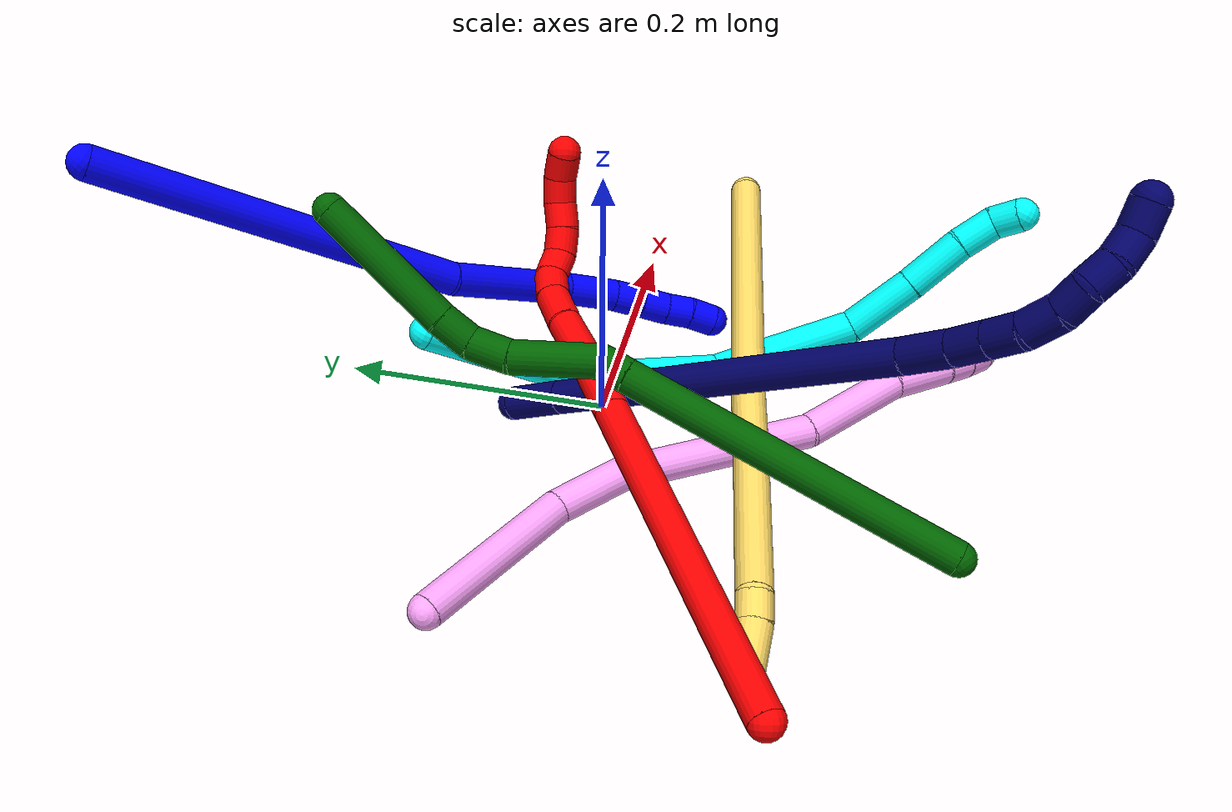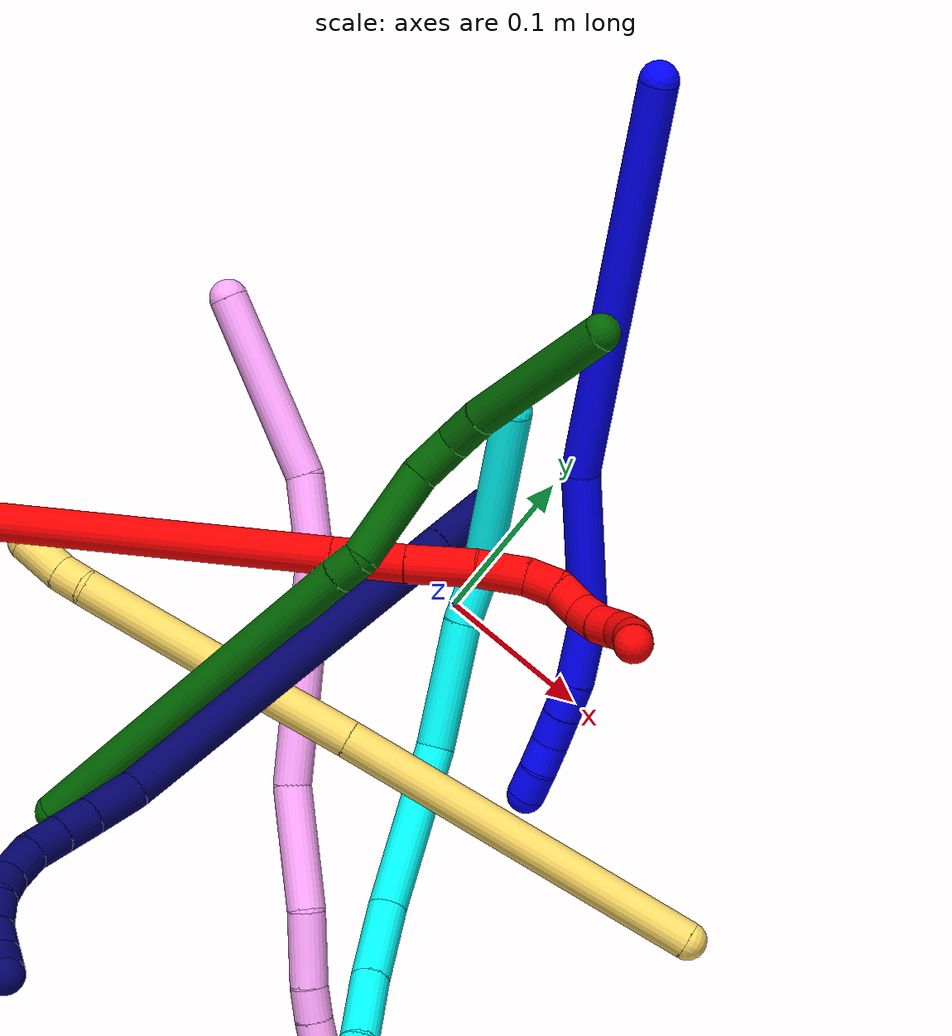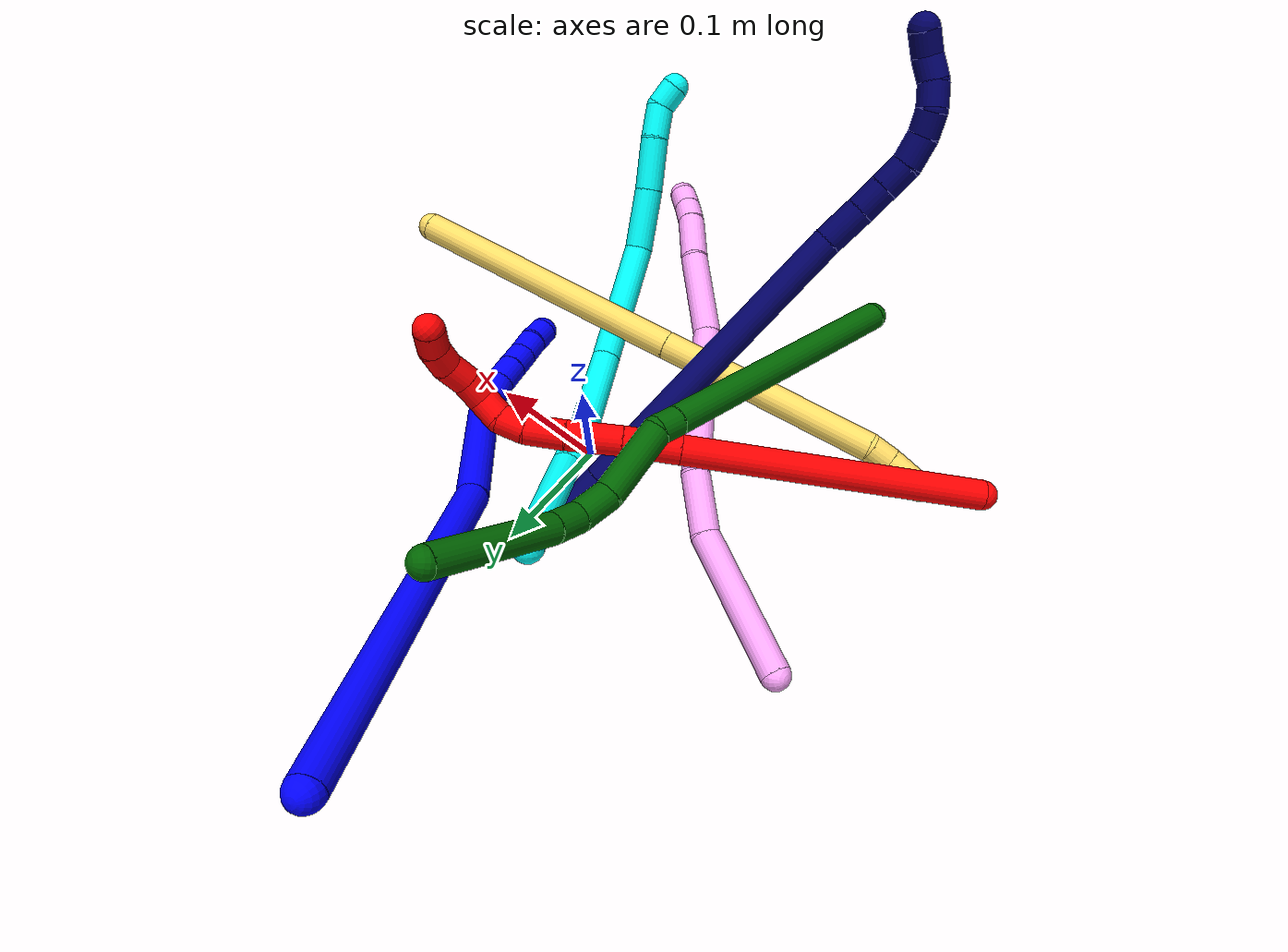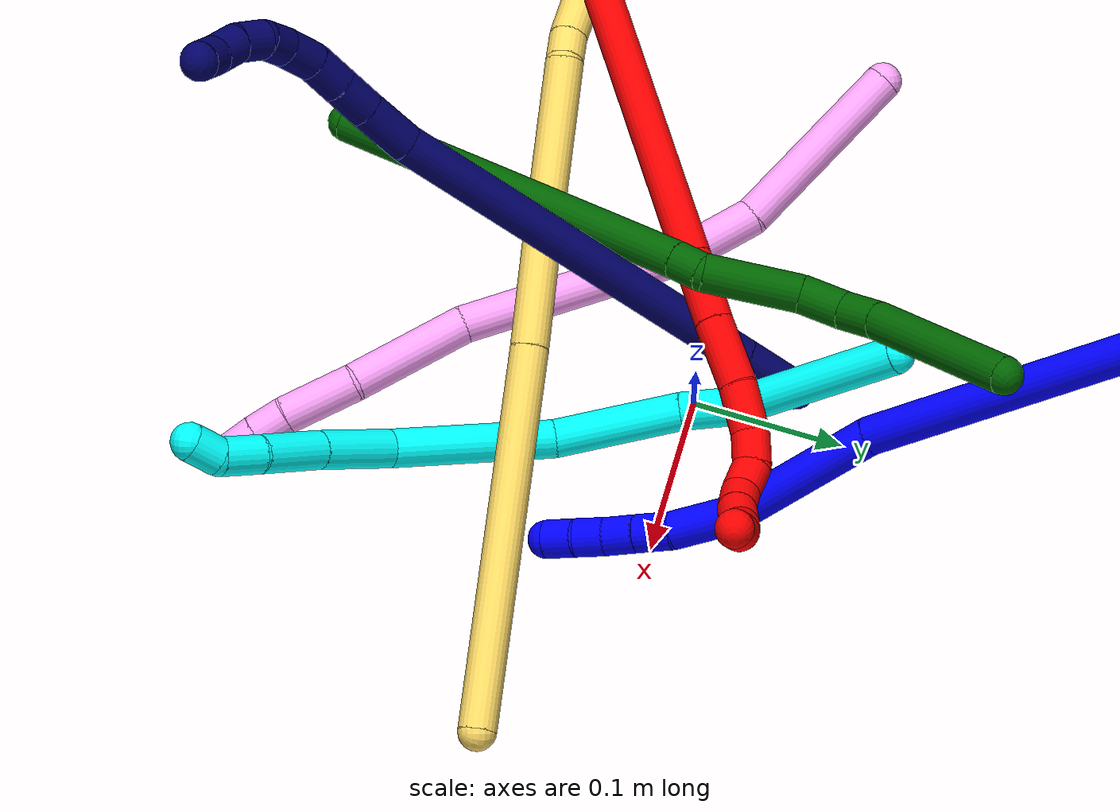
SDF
<sdf version="1.7">
 <world name="default">
  <plugin name="TubeGeneratorPlugin" filename="libtube_generator_plugin.so"/>
  <model name="photoneo_s_sensor">
   <static>1</static>
   <pose>0 0 2 1.57079 1.57079 3.14159</pose>
   <link name="link">
    <inertial><mass>0.1</mass></inertial>
    <sensor name="sensor" type="depth">
     <update_rate>30</update_rate>
     <camera>
      <horizontal_fov>1.22</horizontal_fov>
      <image><width>1920</width><height>1200</height><format>B8G8R8</format></image>
      <clip><near>0.1</near><far>4</far></clip>
      <depth_camera><output>points</output></depth_camera>
     </camera>
     <plugin name="camera_plugin" filename="libgazebo_ros_depth_camera.so">
      <baseline>0.2</baseline>
      <alwaysOn>1</alwaysOn>
      <updateRate>0.0</updateRate>
      <cameraName>camera_ir</cameraName>
      <imageTopicName>/camera/color/image_raw</imageTopicName>
      <cameraInfoTopicName>/camera/color/camera_info</cameraInfoTopicName>
      <depthImageTopicName>/camera/depth/image_raw</depthImageTopicName>
      <depthImageCameraInfoTopicName>/camera/depth/camera_info</depthImageCameraInfoTopicName>
      <pointCloudTopicName>/camera/depth/points</pointCloudTopicName>
      <frameName>fr_optical</frameName>
      <pointCloudCutoff>0.1</pointCloudCutoff>
      <pointCloudCutoffMax>2.0</pointCloudCutoffMax>
      <distortionK1>0</distortionK1>
      <distortionK2>0</distortionK2>
      <distortionK3>0</distortionK3>
      <distortionT1>0</distortionT1>
      <distortionT2>0</distortionT2>
      <CxPrime>0</CxPrime>
      <Cx>0</Cx>
      <Cy>0</Cy>
      <focalLength>0</focalLength>
      <hackBaseline>0</hackBaseline>
     </plugin>
    </sensor>
   </link>
  </model>
  <gravity>0 0 -9.8</gravity>
  <magnetic_field>6e-06 2.3e-05 -4.2e-05</magnetic_field>
  <atmosphere type="adiabatic"/>
  <physics name="default_physics" default="0" type="ode">
   <max_step_size>0.003</max_step_size>
   <real_time_factor>1</real_time_factor>
   <real_time_update_rate>1000</real_time_update_rate>
   <max_contacts>10000</max_contacts>
   <ode>
    <solver>
     <type>quick</type>
     <iters>100</iters>
     <sor>1.3</sor>
     <use_dynamic_moi_rescaling>0</use_dynamic_moi_rescaling>
    </solver>
    <constraints>
     <contact_max_correcting_vel>0</contact_max_correcting_vel>
     <contact_surface_layer>0.001</contact_surface_layer>
     <cfm>0</cfm>
     <erp>0.2</erp>
    </constraints>
   </ode>
  </physics>
  <scene><ambient>0.4 0.4 0.4 1</ambient><background>0.7 0.7 0.7 1</background><shadows>0</shadows></scene>
  <audio><device>default</device></audio>
  <spherical_coordinates>
   <surface_model>EARTH_WGS84</surface_model>
   <latitude_deg>0</latitude_deg>
   <longitude_deg>0</longitude_deg>
   <elevation>0</elevation>
   <heading_deg>0</heading_deg>
  </spherical_coordinates>
  <model name="bin">
   <static>1</static>
   <link name="bottom">
    <collision name="collision-bottom">
     <pose>0 0 -0.01 0 -0 0</pose>
     <geometry><box><size>0.8 0.6 0.02</size></box></geometry>
     <surface>
      <friction><ode><mu>100</mu><mu2>100</mu2></ode></friction>
      <contact><collide_bitmask>65535</collide_bitmask></contact>
     </surface>
    </collision>
   </link>
   <link name="west_wall">
    <collision name="collision-west_wall">
     <pose>-0.41 0 0.1 0 -0 0</pose>
     <geometry><box><size>0.02 0.6 0.2</size></box></geometry>
     <surface>
      <friction><ode><mu>100</mu><mu2>100</mu2></ode></friction>
      <contact><collide_bitmask>65535</collide_bitmask></contact>
     </surface>
    </collision>
   </link>
   <link name="east_wall">
    <collision name="collision-east_wall">
     <pose>0.41 0 0.1 0 -0 0</pose>
     <geometry><box><size>0.02 0.6 0.2</size></box></geometry>
     <surface>
      <friction><ode><mu>100</mu><mu2>100</mu2></ode></friction>
      <contact><collide_bitmask>65535</collide_bitmask></contact>
     </surface>
    </collision>
   </link>
   <link name="south_wall">
    <collision name="collision-south_wall">
     <pose>0 -0.31 0.1 0 -0 0</pose>
     <geometry><box><size>0.8 0.02 0.2</size></box></geometry>
     <surface>
      <friction><ode><mu>100</mu><mu2>100</mu2></ode></friction>
      <contact><collide_bitmask>65535</collide_bitmask></contact>
     </surface>
    </collision>
   </link>
   <link name="north_wall">
    <collision name="collision-north_wall">
     <pose>0 0.31 0.1 0 -0 0</pose>
     <geometry><box><size>0.8 0.02 0.2</size></box></geometry>
     <surface>
      <friction><ode><mu>100</mu><mu2>100</mu2></ode></friction>
      <contact><collide_bitmask>65535</collide_bitmask></contact>
     </surface>
    </collision>
   </link>
  </model>
  <model name="1">
   <static>0</static>
   <link name="1">
    <collision name="collision-cylinder-e_1_1_4">
     <pose>0.022245 -0.037599 -0.127592 2.85502 0.165702 1.04455</pose>
     <geometry><cylinder><radius>0.0125</radius><length>0.269728</length></cylinder></geometry>
     <surface>
      <friction><ode><mu>1.16</mu><mu2>1.16</mu2><slip1>0</slip1><slip2>0</slip2></ode></friction>
      <contact><ode><kp>1e+06</kp><kd>1</kd><max_vel>0</max_vel><min_depth>0.001</min_depth></ode></contact>
     </surface>
    </collision>
    <visual name="visual-cylinder-e_1_1_4">
     <pose>0.022245 -0.037599 -0.127592 2.85502 0.165702 1.04455</pose>
     <geometry><cylinder><radius>0.0125</radius><length>0.269728</length></cylinder></geometry>
     <material><ambient>0 0 1 1</ambient></material>
    </visual>
    <collision name="collision-cylinder-e_2_4_5">
     <pose>0.063211 -0.095388 -0.299077 2.71047 0.369663 1.41346</pose>
     <geometry><cylinder><radius>0.0125</radius><length>0.103628</length></cylinder></geometry>
     <surface>
      <friction><ode><mu>1.16</mu><mu2>1.16</mu2><slip1>0</slip1><slip2>0</slip2></ode></friction>
      <contact><ode><kp>1e+06</kp><kd>1</kd><max_vel>0</max_vel><min_depth>0.001</min_depth></ode></contact>
     </surface>
    </collision>
    <visual name="visual-cylinder-e_2_4_5">
     <pose>0.063211 -0.095388 -0.299077 2.71047 0.369663 1.41346</pose>
     <geometry><cylinder><radius>0.0125</radius><length>0.103628</length></cylinder></geometry>
     <material><ambient>0 0 1 1</ambient></material>
    </visual>
    <collision name="collision-cylinder-e_3_5_6">
     <pose>0.084246 -0.124979 -0.361349 2.66876 0.11165 0.455844</pose>
     <geometry><cylinder><radius>0.0125</radius><length>0.041546</length></cylinder></geometry>
     <surface>
      <friction><ode><mu>1.16</mu><mu2>1.16</mu2><slip1>0</slip1><slip2>0</slip2></ode></friction>
      <contact><ode><kp>1e+06</kp><kd>1</kd><max_vel>0</max_vel><min_depth>0.001</min_depth></ode></contact>
     </surface>
    </collision>
    <visual name="visual-cylinder-e_3_5_6">
     <pose>0.084246 -0.124979 -0.361349 2.66876 0.11165 0.455844</pose>
     <geometry><cylinder><radius>0.0125</radius><length>0.041546</length></cylinder></geometry>
     <material><ambient>0 0 1 1</ambient></material>
    </visual>
    <collision name="collision-cylinder-e_4_6_7">
     <pose>0.08599 -0.139344 -0.390647 2.71499 -0.047545 -0.218676</pose>
     <geometry><cylinder><radius>0.0125</radius><length>0.024016</length></cylinder></geometry>
     <surface>
      <friction><ode><mu>1.16</mu><mu2>1.16</mu2><slip1>0</slip1><slip2>0</slip2></ode></friction>
      <contact><ode><kp>1e+06</kp><kd>1</kd><max_vel>0</max_vel><min_depth>0.001</min_depth></ode></contact>
     </surface>
    </collision>
    <visual name="visual-cylinder-e_4_6_7">
     <pose>0.08599 -0.139344 -0.390647 2.71499 -0.047545 -0.218676</pose>
     <geometry><cylinder><radius>0.0125</radius><length>0.024016</length></cylinder></geometry>
     <material><ambient>0 0 1 1</ambient></material>
    </visual>
    <collision name="collision-cylinder-e_5_7_8">
     <pose>0.085003 -0.148389 -0.411217 2.74144 -0.039653 -0.194946</pose>
     <geometry><cylinder><radius>0.0125</radius><length>0.020974</length></cylinder></geometry>
     <surface>
      <friction><ode><mu>1.16</mu><mu2>1.16</mu2><slip1>0</slip1><slip2>0</slip2></ode></friction>
      <contact><ode><kp>1e+06</kp><kd>1</kd><max_vel>0</max_vel><min_depth>0.001</min_depth></ode></contact>
     </surface>
    </collision>
    <visual name="visual-cylinder-e_5_7_8">
     <pose>0.085003 -0.148389 -0.411217 2.74144 -0.039653 -0.194946</pose>
     <geometry><cylinder><radius>0.0125</radius><length>0.020974</length></cylinder></geometry>
     <material><ambient>0 0 1 1</ambient></material>
    </visual>
    <collision name="collision-cylinder-e_6_8_9">
     <pose>0.083624 -0.15733 -0.429576 2.63262 -0.096353 -0.366539</pose>
     <geometry><cylinder><radius>0.0125</radius><length>0.020037</length></cylinder></geometry>
     <surface>
      <friction><ode><mu>1.16</mu><mu2>1.16</mu2><slip1>0</slip1><slip2>0</slip2></ode></friction>
      <contact><ode><kp>1e+06</kp><kd>1</kd><max_vel>0</max_vel><min_depth>0.001</min_depth></ode></contact>
     </surface>
    </collision>
    <visual name="visual-cylinder-e_6_8_9">
     <pose>0.083624 -0.15733 -0.429576 2.63262 -0.096353 -0.366539</pose>
     <geometry><cylinder><radius>0.0125</radius><length>0.020037</length></cylinder></geometry>
     <material><ambient>0 0 1 1</ambient></material>
    </visual>
    <collision name="collision-cylinder-e_7_9_2">
     <pose>0.081915 -0.16565 -0.447674 2.78842 -0.074276 -0.410567</pose>
     <geometry><cylinder><radius>0.0125</radius><length>0.020072</length></cylinder></geometry>
     <surface>
      <friction><ode><mu>1.16</mu><mu2>1.16</mu2><slip1>0</slip1><slip2>0</slip2></ode></friction>
      <contact><ode><kp>1e+06</kp><kd>1</kd><max_vel>0</max_vel><min_depth>0.001</min_depth></ode></contact>
     </surface>
    </collision>
    <visual name="visual-cylinder-e_7_9_2">
     <pose>0.081915 -0.16565 -0.447674 2.78842 -0.074276 -0.410567</pose>
     <geometry><cylinder><radius>0.0125</radius><length>0.020072</length></cylinder></geometry>
     <material><ambient>0 0 1 1</ambient></material>
    </visual>
    <collision name="collision-sphere-2">
     <pose>0.08117 -0.169112 -0.457065 0 -0 0</pose>
     <geometry><sphere><radius>0.0125</radius></sphere></geometry>
     <surface>
      <friction><ode><mu>1.16</mu><mu2>1.16</mu2><slip1>0</slip1><slip2>0</slip2></ode></friction>
      <contact><ode><kp>1e+06</kp><kd>1</kd><max_vel>0</max_vel><min_depth>0.001</min_depth></ode></contact>
     </surface>
    </collision>
    <visual name="visual-sphere-2">
     <pose>0.08117 -0.169112 -0.457065 0 -0 0</pose>
     <geometry><sphere><radius>0.0125</radius></sphere></geometry>
     <material><ambient>0 0 1 1</ambient></material>
    </visual>
    <collision name="collision-sphere-9">
     <pose>0.08266 -0.162189 -0.438284 0 -0 0</pose>
     <geometry><sphere><radius>0.0125</radius></sphere></geometry>
     <surface>
      <friction><ode><mu>1.16</mu><mu2>1.16</mu2><slip1>0</slip1><slip2>0</slip2></ode></friction>
      <contact><ode><kp>1e+06</kp><kd>1</kd><max_vel>0</max_vel><min_depth>0.001</min_depth></ode></contact>
     </surface>
    </collision>
    <visual name="visual-sphere-9">
     <pose>0.08266 -0.162189 -0.438284 0 -0 0</pose>
     <geometry><sphere><radius>0.0125</radius></sphere></geometry>
     <material><ambient>0 0 1 1</ambient></material>
    </visual>
    <collision name="collision-sphere-4">
     <pose>0.04449 -0.075197 -0.255184 0 -0 0</pose>
     <geometry><sphere><radius>0.0125</radius></sphere></geometry>
     <surface>
      <friction><ode><mu>1.16</mu><mu2>1.16</mu2><slip1>0</slip1><slip2>0</slip2></ode></friction>
      <contact><ode><kp>1e+06</kp><kd>1</kd><max_vel>0</max_vel><min_depth>0.001</min_depth></ode></contact>
     </surface>
    </collision>
    <visual name="visual-sphere-4">
     <pose>0.04449 -0.075197 -0.255184 0 -0 0</pose>
     <geometry><sphere><radius>0.0125</radius></sphere></geometry>
     <material><ambient>0 0 1 1</ambient></material>
    </visual>
    <collision name="collision-sphere-1">
     <geometry><sphere><radius>0.0125</radius></sphere></geometry>
     <surface>
      <friction><ode><mu>1.16</mu><mu2>1.16</mu2><slip1>0</slip1><slip2>0</slip2></ode></friction>
      <contact><ode><kp>1e+06</kp><kd>1</kd><max_vel>0</max_vel><min_depth>0.001</min_depth></ode></contact>
     </surface>
    </collision>
    <visual name="visual-sphere-1">
     <geometry><sphere><radius>0.0125</radius></sphere></geometry>
     <material><ambient>0 0 1 1</ambient></material>
    </visual>
    <collision name="collision-sphere-8">
     <pose>0.084587 -0.152471 -0.420868 0 -0 0</pose>
     <geometry><sphere><radius>0.0125</radius></sphere></geometry>
     <surface>
      <friction><ode><mu>1.16</mu><mu2>1.16</mu2><slip1>0</slip1><slip2>0</slip2></ode></friction>
      <contact><ode><kp>1e+06</kp><kd>1</kd><max_vel>0</max_vel><min_depth>0.001</min_depth></ode></contact>
     </surface>
    </collision>
    <visual name="visual-sphere-8">
     <pose>0.084587 -0.152471 -0.420868 0 -0 0</pose>
     <geometry><sphere><radius>0.0125</radius></sphere></geometry>
     <material><ambient>0 0 1 1</ambient></material>
    </visual>
    <collision name="collision-sphere-5">
     <pose>0.081931 -0.115578 -0.34297 0 -0 0</pose>
     <geometry><sphere><radius>0.0125</radius></sphere></geometry>
     <surface>
      <friction><ode><mu>1.16</mu><mu2>1.16</mu2><slip1>0</slip1><slip2>0</slip2></ode></friction>
      <contact><ode><kp>1e+06</kp><kd>1</kd><max_vel>0</max_vel><min_depth>0.001</min_depth></ode></contact>
     </surface>
    </collision>
    <visual name="visual-sphere-5">
     <pose>0.081931 -0.115578 -0.34297 0 -0 0</pose>
     <geometry><sphere><radius>0.0125</radius></sphere></geometry>
     <material><ambient>0 0 1 1</ambient></material>
    </visual>
    <collision name="collision-sphere-6">
     <pose>0.08656 -0.134381 -0.379728 0 -0 0</pose>
     <geometry><sphere><radius>0.0125</radius></sphere></geometry>
     <surface>
      <friction><ode><mu>1.16</mu><mu2>1.16</mu2><slip1>0</slip1><slip2>0</slip2></ode></friction>
      <contact><ode><kp>1e+06</kp><kd>1</kd><max_vel>0</max_vel><min_depth>0.001</min_depth></ode></contact>
     </surface>
    </collision>
    <visual name="visual-sphere-6">
     <pose>0.08656 -0.134381 -0.379728 0 -0 0</pose>
     <geometry><sphere><radius>0.0125</radius></sphere></geometry>
     <material><ambient>0 0 1 1</ambient></material>
    </visual>
    <collision name="collision-sphere-7">
     <pose>0.085419 -0.144307 -0.401566 0 -0 0</pose>
     <geometry><sphere><radius>0.0125</radius></sphere></geometry>
     <surface>
      <friction><ode><mu>1.16</mu><mu2>1.16</mu2><slip1>0</slip1><slip2>0</slip2></ode></friction>
      <contact><ode><kp>1e+06</kp><kd>1</kd><max_vel>0</max_vel><min_depth>0.001</min_depth></ode></contact>
     </surface>
    </collision>
    <visual name="visual-sphere-7">
     <pose>0.085419 -0.144307 -0.401566 0 -0 0</pose>
     <geometry><sphere><radius>0.0125</radius></sphere></geometry>
     <material><ambient>0 0 1 1</ambient></material>
    </visual>
    <inertial>
     <pose>0.046437 -0.076309 -0.23204 0 -0 0</pose>
     <mass>0.5</mass>
     <inertia>
      <ixx>0.002343</ixx>
      <ixy>0</ixy>
      <ixz>0</ixz>
      <iyy>0.000743</iyy>
      <iyz>0</iyz>
      <izz>0.00016</izz>
     </inertia>
    </inertial>
   </link>
   <pose>-0.104987 0.320848 0.228317 -0.785567 0.234089 0.444727</pose>
  </model>
  <model name="2">
   <static>0</static>
   <link name="2">
    <collision name="collision-cylinder-e_1_1_4">
     <pose>0.089248 0.001063 0.08856 -0.012002 0.789234 -0.004999</pose>
     <geometry><cylinder><radius>0.0125</radius><length>0.251469</length></cylinder></geometry>
     <surface>
      <friction><ode><mu>1.16</mu><mu2>1.16</mu2><slip1>0</slip1><slip2>0</slip2></ode></friction>
      <contact><ode><kp>1e+06</kp><kd>1</kd><max_vel>0</max_vel><min_depth>0.001</min_depth></ode></contact>
     </surface>
    </collision>
    <visual name="visual-cylinder-e_1_1_4">
     <pose>0.089248 0.001063 0.08856 -0.012002 0.789234 -0.004999</pose>
     <geometry><cylinder><radius>0.0125</radius><length>0.251469</length></cylinder></geometry>
     <material><ambient>1 0 0 1</ambient></material>
    </visual>
    <collision name="collision-cylinder-e_2_4_5">
     <pose>0.195399 0.002199 0.193785 -0.004354 0.792471 -0.001822</pose>
     <geometry><cylinder><radius>0.0125</radius><length>0.047474</length></cylinder></geometry>
     <surface>
      <friction><ode><mu>1.16</mu><mu2>1.16</mu2><slip1>0</slip1><slip2>0</slip2></ode></friction>
      <contact><ode><kp>1e+06</kp><kd>1</kd><max_vel>0</max_vel><min_depth>0.001</min_depth></ode></contact>
     </surface>
    </collision>
    <visual name="visual-cylinder-e_2_4_5">
     <pose>0.195399 0.002199 0.193785 -0.004354 0.792471 -0.001822</pose>
     <geometry><cylinder><radius>0.0125</radius><length>0.047474</length></cylinder></geometry>
     <material><ambient>1 0 0 1</ambient></material>
    </visual>
    <collision name="collision-cylinder-e_3_5_6">
     <pose>0.228975 0.002977 0.225557 -0.046688 0.834079 -0.020687</pose>
     <geometry><cylinder><radius>0.0125</radius><length>0.045021</length></cylinder></geometry>
     <surface>
      <friction><ode><mu>1.16</mu><mu2>1.16</mu2><slip1>0</slip1><slip2>0</slip2></ode></friction>
      <contact><ode><kp>1e+06</kp><kd>1</kd><max_vel>0</max_vel><min_depth>0.001</min_depth></ode></contact>
     </surface>
    </collision>
    <visual name="visual-cylinder-e_3_5_6">
     <pose>0.228975 0.002977 0.225557 -0.046688 0.834079 -0.020687</pose>
     <geometry><cylinder><radius>0.0125</radius><length>0.045021</length></cylinder></geometry>
     <material><ambient>1 0 0 1</ambient></material>
    </visual>
    <collision name="collision-cylinder-e_4_6_7">
     <pose>0.25796 0.002283 0.251131 0.132955 0.861867 0.061197</pose>
     <geometry><cylinder><radius>0.0125</radius><length>0.032441</length></cylinder></geometry>
     <surface>
      <friction><ode><mu>1.16</mu><mu2>1.16</mu2><slip1>0</slip1><slip2>0</slip2></ode></friction>
      <contact><ode><kp>1e+06</kp><kd>1</kd><max_vel>0</max_vel><min_depth>0.001</min_depth></ode></contact>
     </surface>
    </collision>
    <visual name="visual-cylinder-e_4_6_7">
     <pose>0.25796 0.002283 0.251131 0.132955 0.861867 0.061197</pose>
     <geometry><cylinder><radius>0.0125</radius><length>0.032441</length></cylinder></geometry>
     <material><ambient>1 0 0 1</ambient></material>
    </visual>
    <collision name="collision-cylinder-e_5_7_8">
     <pose>0.276851 -0.001586 0.270051 0.284239 0.641591 0.095014</pose>
     <geometry><cylinder><radius>0.0125</radius><length>0.021984</length></cylinder></geometry>
     <surface>
      <friction><ode><mu>1.16</mu><mu2>1.16</mu2><slip1>0</slip1><slip2>0</slip2></ode></friction>
      <contact><ode><kp>1e+06</kp><kd>1</kd><max_vel>0</max_vel><min_depth>0.001</min_depth></ode></contact>
     </surface>
    </collision>
    <visual name="visual-cylinder-e_5_7_8">
     <pose>0.276851 -0.001586 0.270051 0.284239 0.641591 0.095014</pose>
     <geometry><cylinder><radius>0.0125</radius><length>0.021984</length></cylinder></geometry>
     <material><ambient>1 0 0 1</ambient></material>
    </visual>
    <collision name="collision-cylinder-e_6_8_9">
     <pose>0.28601 -0.009023 0.287214 0.518264 0.251939 0.067117</pose>
     <geometry><cylinder><radius>0.0125</radius><length>0.020709</length></cylinder></geometry>
     <surface>
      <friction><ode><mu>1.16</mu><mu2>1.16</mu2><slip1>0</slip1><slip2>0</slip2></ode></friction>
      <contact><ode><kp>1e+06</kp><kd>1</kd><max_vel>0</max_vel><min_depth>0.001</min_depth></ode></contact>
     </surface>
    </collision>
    <visual name="visual-cylinder-e_6_8_9">
     <pose>0.28601 -0.009023 0.287214 0.518264 0.251939 0.067117</pose>
     <geometry><cylinder><radius>0.0125</radius><length>0.020709</length></cylinder></geometry>
     <material><ambient>1 0 0 1</ambient></material>
    </visual>
    <collision name="collision-cylinder-e_7_9_10">
     <pose>0.28841 -0.014799 0.306165 0.078742 -0.017656 -0.000696</pose>
     <geometry><cylinder><radius>0.0125</radius><length>0.020546</length></cylinder></geometry>
     <surface>
      <friction><ode><mu>1.16</mu><mu2>1.16</mu2><slip1>0</slip1><slip2>0</slip2></ode></friction>
      <contact><ode><kp>1e+06</kp><kd>1</kd><max_vel>0</max_vel><min_depth>0.001</min_depth></ode></contact>
     </surface>
    </collision>
    <visual name="visual-cylinder-e_7_9_10">
     <pose>0.28841 -0.014799 0.306165 0.078742 -0.017656 -0.000696</pose>
     <geometry><cylinder><radius>0.0125</radius><length>0.020546</length></cylinder></geometry>
     <material><ambient>1 0 0 1</ambient></material>
    </visual>
    <collision name="collision-cylinder-e_8_10_11">
     <pose>0.288994 -0.014454 0.326464 -0.11409 0.075414 -0.004309</pose>
     <geometry><cylinder><radius>0.0125</radius><length>0.020308</length></cylinder></geometry>
     <surface>
      <friction><ode><mu>1.16</mu><mu2>1.16</mu2><slip1>0</slip1><slip2>0</slip2></ode></friction>
      <contact><ode><kp>1e+06</kp><kd>1</kd><max_vel>0</max_vel><min_depth>0.001</min_depth></ode></contact>
     </surface>
    </collision>
    <visual name="visual-cylinder-e_8_10_11">
     <pose>0.288994 -0.014454 0.326464 -0.11409 0.075414 -0.004309</pose>
     <geometry><cylinder><radius>0.0125</radius><length>0.020308</length></cylinder></geometry>
     <material><ambient>1 0 0 1</ambient></material>
    </visual>
    <collision name="collision-cylinder-e_9_11_12">
     <pose>0.287087 -0.01154 0.346009 -0.18362 -0.270192 0.025027</pose>
     <geometry><cylinder><radius>0.0125</radius><length>0.020023</length></cylinder></geometry>
     <surface>
      <friction><ode><mu>1.16</mu><mu2>1.16</mu2><slip1>0</slip1><slip2>0</slip2></ode></friction>
      <contact><ode><kp>1e+06</kp><kd>1</kd><max_vel>0</max_vel><min_depth>0.001</min_depth></ode></contact>
     </surface>
    </collision>
    <visual name="visual-cylinder-e_9_11_12">
     <pose>0.287087 -0.01154 0.346009 -0.18362 -0.270192 0.025027</pose>
     <geometry><cylinder><radius>0.0125</radius><length>0.020023</length></cylinder></geometry>
     <material><ambient>1 0 0 1</ambient></material>
    </visual>
    <collision name="collision-cylinder-e_10_12_2">
     <pose>0.278766 -0.008208 0.363612 -0.191108 -0.599366 0.059213</pose>
     <geometry><cylinder><radius>0.0125</radius><length>0.020025</length></cylinder></geometry>
     <surface>
      <friction><ode><mu>1.16</mu><mu2>1.16</mu2><slip1>0</slip1><slip2>0</slip2></ode></friction>
      <contact><ode><kp>1e+06</kp><kd>1</kd><max_vel>0</max_vel><min_depth>0.001</min_depth></ode></contact>
     </surface>
    </collision>
    <visual name="visual-cylinder-e_10_12_2">
     <pose>0.278766 -0.008208 0.363612 -0.191108 -0.599366 0.059213</pose>
     <geometry><cylinder><radius>0.0125</radius><length>0.020025</length></cylinder></geometry>
     <material><ambient>1 0 0 1</ambient></material>
    </visual>
    <collision name="collision-sphere-2">
     <pose>0.273118 -0.006637 0.371729 0 -0 0</pose>
     <geometry><sphere><radius>0.0125</radius></sphere></geometry>
     <surface>
      <friction><ode><mu>1.16</mu><mu2>1.16</mu2><slip1>0</slip1><slip2>0</slip2></ode></friction>
      <contact><ode><kp>1e+06</kp><kd>1</kd><max_vel>0</max_vel><min_depth>0.001</min_depth></ode></contact>
     </surface>
    </collision>
    <visual name="visual-sphere-2">
     <pose>0.273118 -0.006637 0.371729 0 -0 0</pose>
     <geometry><sphere><radius>0.0125</radius></sphere></geometry>
     <material><ambient>1 0 0 1</ambient></material>
    </visual>
    <collision name="collision-sphere-12">
     <pose>0.284414 -0.009778 0.355495 0 -0 0</pose>
     <geometry><sphere><radius>0.0125</radius></sphere></geometry>
     <surface>
      <friction><ode><mu>1.16</mu><mu2>1.16</mu2><slip1>0</slip1><slip2>0</slip2></ode></friction>
      <contact><ode><kp>1e+06</kp><kd>1</kd><max_vel>0</max_vel><min_depth>0.001</min_depth></ode></contact>
     </surface>
    </collision>
    <visual name="visual-sphere-12">
     <pose>0.284414 -0.009778 0.355495 0 -0 0</pose>
     <geometry><sphere><radius>0.0125</radius></sphere></geometry>
     <material><ambient>1 0 0 1</ambient></material>
    </visual>
    <collision name="collision-sphere-11">
     <pose>0.289759 -0.013301 0.336523 0 -0 0</pose>
     <geometry><sphere><radius>0.0125</radius></sphere></geometry>
     <surface>
      <friction><ode><mu>1.16</mu><mu2>1.16</mu2><slip1>0</slip1><slip2>0</slip2></ode></friction>
      <contact><ode><kp>1e+06</kp><kd>1</kd><max_vel>0</max_vel><min_depth>0.001</min_depth></ode></contact>
     </surface>
    </collision>
    <visual name="visual-sphere-11">
     <pose>0.289759 -0.013301 0.336523 0 -0 0</pose>
     <geometry><sphere><radius>0.0125</radius></sphere></geometry>
     <material><ambient>1 0 0 1</ambient></material>
    </visual>
    <collision name="collision-sphere-10">
     <pose>0.288229 -0.015607 0.316404 0 -0 0</pose>
     <geometry><sphere><radius>0.0125</radius></sphere></geometry>
     <surface>
      <friction><ode><mu>1.16</mu><mu2>1.16</mu2><slip1>0</slip1><slip2>0</slip2></ode></friction>
      <contact><ode><kp>1e+06</kp><kd>1</kd><max_vel>0</max_vel><min_depth>0.001</min_depth></ode></contact>
     </surface>
    </collision>
    <visual name="visual-sphere-10">
     <pose>0.288229 -0.015607 0.316404 0 -0 0</pose>
     <geometry><sphere><radius>0.0125</radius></sphere></geometry>
     <material><ambient>1 0 0 1</ambient></material>
    </visual>
    <collision name="collision-sphere-9">
     <pose>0.288591 -0.013991 0.295925 0 -0 0</pose>
     <geometry><sphere><radius>0.0125</radius></sphere></geometry>
     <surface>
      <friction><ode><mu>1.16</mu><mu2>1.16</mu2><slip1>0</slip1><slip2>0</slip2></ode></friction>
      <contact><ode><kp>1e+06</kp><kd>1</kd><max_vel>0</max_vel><min_depth>0.001</min_depth></ode></contact>
     </surface>
    </collision>
    <visual name="visual-sphere-9">
     <pose>0.288591 -0.013991 0.295925 0 -0 0</pose>
     <geometry><sphere><radius>0.0125</radius></sphere></geometry>
     <material><ambient>1 0 0 1</ambient></material>
    </visual>
    <collision name="collision-sphere-4">
     <pose>0.178496 0.002126 0.177119 0 -0 0</pose>
     <geometry><sphere><radius>0.0125</radius></sphere></geometry>
     <surface>
      <friction><ode><mu>1.16</mu><mu2>1.16</mu2><slip1>0</slip1><slip2>0</slip2></ode></friction>
      <contact><ode><kp>1e+06</kp><kd>1</kd><max_vel>0</max_vel><min_depth>0.001</min_depth></ode></contact>
     </surface>
    </collision>
    <visual name="visual-sphere-4">
     <pose>0.178496 0.002126 0.177119 0 -0 0</pose>
     <geometry><sphere><radius>0.0125</radius></sphere></geometry>
     <material><ambient>1 0 0 1</ambient></material>
    </visual>
    <collision name="collision-sphere-1">
     <geometry><sphere><radius>0.0125</radius></sphere></geometry>
     <surface>
      <friction><ode><mu>1.16</mu><mu2>1.16</mu2><slip1>0</slip1><slip2>0</slip2></ode></friction>
      <contact><ode><kp>1e+06</kp><kd>1</kd><max_vel>0</max_vel><min_depth>0.001</min_depth></ode></contact>
     </surface>
    </collision>
    <visual name="visual-sphere-1">
     <geometry><sphere><radius>0.0125</radius></sphere></geometry>
     <material><ambient>1 0 0 1</ambient></material>
    </visual>
    <collision name="collision-sphere-8">
     <pose>0.283429 -0.004056 0.278503 0 -0 0</pose>
     <geometry><sphere><radius>0.0125</radius></sphere></geometry>
     <surface>
      <friction><ode><mu>1.16</mu><mu2>1.16</mu2><slip1>0</slip1><slip2>0</slip2></ode></friction>
      <contact><ode><kp>1e+06</kp><kd>1</kd><max_vel>0</max_vel><min_depth>0.001</min_depth></ode></contact>
     </surface>
    </collision>
    <visual name="visual-sphere-8">
     <pose>0.283429 -0.004056 0.278503 0 -0 0</pose>
     <geometry><sphere><radius>0.0125</radius></sphere></geometry>
     <material><ambient>1 0 0 1</ambient></material>
    </visual>
    <collision name="collision-sphere-5">
     <pose>0.212302 0.002271 0.21045 0 -0 0</pose>
     <geometry><sphere><radius>0.0125</radius></sphere></geometry>
     <surface>
      <friction><ode><mu>1.16</mu><mu2>1.16</mu2><slip1>0</slip1><slip2>0</slip2></ode></friction>
      <contact><ode><kp>1e+06</kp><kd>1</kd><max_vel>0</max_vel><min_depth>0.001</min_depth></ode></contact>
     </surface>
    </collision>
    <visual name="visual-sphere-5">
     <pose>0.212302 0.002271 0.21045 0 -0 0</pose>
     <geometry><sphere><radius>0.0125</radius></sphere></geometry>
     <material><ambient>1 0 0 1</ambient></material>
    </visual>
    <collision name="collision-sphere-6">
     <pose>0.245648 0.003683 0.240664 0 -0 0</pose>
     <geometry><sphere><radius>0.0125</radius></sphere></geometry>
     <surface>
      <friction><ode><mu>1.16</mu><mu2>1.16</mu2><slip1>0</slip1><slip2>0</slip2></ode></friction>
      <contact><ode><kp>1e+06</kp><kd>1</kd><max_vel>0</max_vel><min_depth>0.001</min_depth></ode></contact>
     </surface>
    </collision>
    <visual name="visual-sphere-6">
     <pose>0.245648 0.003683 0.240664 0 -0 0</pose>
     <geometry><sphere><radius>0.0125</radius></sphere></geometry>
     <material><ambient>1 0 0 1</ambient></material>
    </visual>
    <collision name="collision-sphere-7">
     <pose>0.270272 0.000883 0.261598 0 -0 0</pose>
     <geometry><sphere><radius>0.0125</radius></sphere></geometry>
     <surface>
      <friction><ode><mu>1.16</mu><mu2>1.16</mu2><slip1>0</slip1><slip2>0</slip2></ode></friction>
      <contact><ode><kp>1e+06</kp><kd>1</kd><max_vel>0</max_vel><min_depth>0.001</min_depth></ode></contact>
     </surface>
    </collision>
    <visual name="visual-sphere-7">
     <pose>0.270272 0.000883 0.261598 0 -0 0</pose>
     <geometry><sphere><radius>0.0125</radius></sphere></geometry>
     <material><ambient>1 0 0 1</ambient></material>
    </visual>
    <inertial>
     <pose>0.171062 -0.00127 0.177572 0 -0 0</pose>
     <mass>0.5</mass>
     <inertia>
      <ixx>0.000982</ixx>
      <ixy>0</ixy>
      <ixz>0</ixz>
      <iyy>0.001363</iyy>
      <iyz>0</iyz>
      <izz>-0.000947</izz>
     </inertia>
    </inertial>
   </link>
   <pose>-0.285719 -0.163369 0.026851 0.4256 0.579967 0.879985</pose>
  </model>
  <model name="3">
   <static>0</static>
   <link name="3">
    <collision name="collision-cylinder-e_1_1_4">
     <pose>-0.001387 -0.022854 0.053399 0.404406 -0.023867 -0.004893</pose>
     <geometry><cylinder><radius>0.0125</radius><length>0.116201</length></cylinder></geometry>
     <surface>
      <friction><ode><mu>1.16</mu><mu2>1.16</mu2><slip1>0</slip1><slip2>0</slip2></ode></friction>
      <contact><ode><kp>1e+06</kp><kd>1</kd><max_vel>0</max_vel><min_depth>0.001</min_depth></ode></contact>
     </surface>
    </collision>
    <visual name="visual-cylinder-e_1_1_4">
     <pose>-0.001387 -0.022854 0.053399 0.404406 -0.023867 -0.004893</pose>
     <geometry><cylinder><radius>0.0125</radius><length>0.116201</length></cylinder></geometry>
     <material><ambient>0.003922 1 0.996078 1</ambient></material>
    </visual>
    <collision name="collision-cylinder-e_2_4_5">
     <pose>0.003247 -0.05005 0.123797 0.250008 0.330556 0.041914</pose>
     <geometry><cylinder><radius>0.0125</radius><length>0.037098</length></cylinder></geometry>
     <surface>
      <friction><ode><mu>1.16</mu><mu2>1.16</mu2><slip1>0</slip1><slip2>0</slip2></ode></friction>
      <contact><ode><kp>1e+06</kp><kd>1</kd><max_vel>0</max_vel><min_depth>0.001</min_depth></ode></contact>
     </surface>
    </collision>
    <visual name="visual-cylinder-e_2_4_5">
     <pose>0.003247 -0.05005 0.123797 0.250008 0.330556 0.041914</pose>
     <geometry><cylinder><radius>0.0125</radius><length>0.037098</length></cylinder></geometry>
     <material><ambient>0.003922 1 0.996078 1</ambient></material>
    </visual>
    <collision name="collision-cylinder-e_3_5_6">
     <pose>0.024852 -0.06901 0.176979 0.383991 0.379937 0.074723</pose>
     <geometry><cylinder><radius>0.0125</radius><length>0.084043</length></cylinder></geometry>
     <surface>
      <friction><ode><mu>1.16</mu><mu2>1.16</mu2><slip1>0</slip1><slip2>0</slip2></ode></friction>
      <contact><ode><kp>1e+06</kp><kd>1</kd><max_vel>0</max_vel><min_depth>0.001</min_depth></ode></contact>
     </surface>
    </collision>
    <visual name="visual-cylinder-e_3_5_6">
     <pose>0.024852 -0.06901 0.176979 0.383991 0.379937 0.074723</pose>
     <geometry><cylinder><radius>0.0125</radius><length>0.084043</length></cylinder></geometry>
     <material><ambient>0.003922 1 0.996078 1</ambient></material>
    </visual>
    <collision name="collision-cylinder-e_4_6_7">
     <pose>0.078587 -0.094205 0.251141 0.271561 0.769002 0.110453</pose>
     <geometry><cylinder><radius>0.0125</radius><length>0.10972</length></cylinder></geometry>
     <surface>
      <friction><ode><mu>1.16</mu><mu2>1.16</mu2><slip1>0</slip1><slip2>0</slip2></ode></friction>
      <contact><ode><kp>1e+06</kp><kd>1</kd><max_vel>0</max_vel><min_depth>0.001</min_depth></ode></contact>
     </surface>
    </collision>
    <visual name="visual-cylinder-e_4_6_7">
     <pose>0.078587 -0.094205 0.251141 0.271561 0.769002 0.110453</pose>
     <geometry><cylinder><radius>0.0125</radius><length>0.10972</length></cylinder></geometry>
     <material><ambient>0.003922 1 0.996078 1</ambient></material>
    </visual>
    <collision name="collision-cylinder-e_5_7_8">
     <pose>0.141919 -0.108286 0.299918 0.313995 1.14719 0.203831</pose>
     <geometry><cylinder><radius>0.0125</radius><length>0.055246</length></cylinder></geometry>
     <surface>
      <friction><ode><mu>1.16</mu><mu2>1.16</mu2><slip1>0</slip1><slip2>0</slip2></ode></friction>
      <contact><ode><kp>1e+06</kp><kd>1</kd><max_vel>0</max_vel><min_depth>0.001</min_depth></ode></contact>
     </surface>
    </collision>
    <visual name="visual-cylinder-e_5_7_8">
     <pose>0.141919 -0.108286 0.299918 0.313995 1.14719 0.203831</pose>
     <geometry><cylinder><radius>0.0125</radius><length>0.055246</length></cylinder></geometry>
     <material><ambient>0.003922 1 0.996078 1</ambient></material>
    </visual>
    <collision name="collision-cylinder-e_6_8_9">
     <pose>0.188592 -0.115598 0.318684 0.445528 1.18103 0.301377</pose>
     <geometry><cylinder><radius>0.0125</radius><length>0.046469</length></cylinder></geometry>
     <surface>
      <friction><ode><mu>1.16</mu><mu2>1.16</mu2><slip1>0</slip1><slip2>0</slip2></ode></friction>
      <contact><ode><kp>1e+06</kp><kd>1</kd><max_vel>0</max_vel><min_depth>0.001</min_depth></ode></contact>
     </surface>
    </collision>
    <visual name="visual-cylinder-e_6_8_9">
     <pose>0.188592 -0.115598 0.318684 0.445528 1.18103 0.301377</pose>
     <geometry><cylinder><radius>0.0125</radius><length>0.046469</length></cylinder></geometry>
     <material><ambient>0.003922 1 0.996078 1</ambient></material>
    </visual>
    <collision name="collision-cylinder-e_7_9_10">
     <pose>0.222903 -0.121944 0.333495 0.355625 1.05304 0.20816</pose>
     <geometry><cylinder><radius>0.0125</radius><length>0.029504</length></cylinder></geometry>
     <surface>
      <friction><ode><mu>1.16</mu><mu2>1.16</mu2><slip1>0</slip1><slip2>0</slip2></ode></friction>
      <contact><ode><kp>1e+06</kp><kd>1</kd><max_vel>0</max_vel><min_depth>0.001</min_depth></ode></contact>
     </surface>
    </collision>
    <visual name="visual-cylinder-e_7_9_10">
     <pose>0.222903 -0.121944 0.333495 0.355625 1.05304 0.20816</pose>
     <geometry><cylinder><radius>0.0125</radius><length>0.029504</length></cylinder></geometry>
     <material><ambient>0.003922 1 0.996078 1</ambient></material>
    </visual>
    <collision name="collision-cylinder-e_8_10_2">
     <pose>0.244204 -0.121105 0.346215 -0.522229 0.896573 -0.25563</pose>
     <geometry><cylinder><radius>0.0125</radius><length>0.021718</length></cylinder></geometry>
     <surface>
      <friction><ode><mu>1.16</mu><mu2>1.16</mu2><slip1>0</slip1><slip2>0</slip2></ode></friction>
      <contact><ode><kp>1e+06</kp><kd>1</kd><max_vel>0</max_vel><min_depth>0.001</min_depth></ode></contact>
     </surface>
    </collision>
    <visual name="visual-cylinder-e_8_10_2">
     <pose>0.244204 -0.121105 0.346215 -0.522229 0.896573 -0.25563</pose>
     <geometry><cylinder><radius>0.0125</radius><length>0.021718</length></cylinder></geometry>
     <material><ambient>0.003922 1 0.996078 1</ambient></material>
    </visual>
    <collision name="collision-sphere-2">
     <pose>0.252687 -0.117723 0.35209 0 -0 0</pose>
     <geometry><sphere><radius>0.0125</radius></sphere></geometry>
     <surface>
      <friction><ode><mu>1.16</mu><mu2>1.16</mu2><slip1>0</slip1><slip2>0</slip2></ode></friction>
      <contact><ode><kp>1e+06</kp><kd>1</kd><max_vel>0</max_vel><min_depth>0.001</min_depth></ode></contact>
     </surface>
    </collision>
    <visual name="visual-sphere-2">
     <pose>0.252687 -0.117723 0.35209 0 -0 0</pose>
     <geometry><sphere><radius>0.0125</radius></sphere></geometry>
     <material><ambient>0.003922 1 0.996078 1</ambient></material>
    </visual>
    <collision name="collision-sphere-10">
     <pose>0.235721 -0.124486 0.340339 0 -0 0</pose>
     <geometry><sphere><radius>0.0125</radius></sphere></geometry>
     <surface>
      <friction><ode><mu>1.16</mu><mu2>1.16</mu2><slip1>0</slip1><slip2>0</slip2></ode></friction>
      <contact><ode><kp>1e+06</kp><kd>1</kd><max_vel>0</max_vel><min_depth>0.001</min_depth></ode></contact>
     </surface>
    </collision>
    <visual name="visual-sphere-10">
     <pose>0.235721 -0.124486 0.340339 0 -0 0</pose>
     <geometry><sphere><radius>0.0125</radius></sphere></geometry>
     <material><ambient>0.003922 1 0.996078 1</ambient></material>
    </visual>
    <collision name="collision-sphere-9">
     <pose>0.210084 -0.119402 0.32665 0 -0 0</pose>
     <geometry><sphere><radius>0.0125</radius></sphere></geometry>
     <surface>
      <friction><ode><mu>1.16</mu><mu2>1.16</mu2><slip1>0</slip1><slip2>0</slip2></ode></friction>
      <contact><ode><kp>1e+06</kp><kd>1</kd><max_vel>0</max_vel><min_depth>0.001</min_depth></ode></contact>
     </surface>
    </collision>
    <visual name="visual-sphere-9">
     <pose>0.210084 -0.119402 0.32665 0 -0 0</pose>
     <geometry><sphere><radius>0.0125</radius></sphere></geometry>
     <material><ambient>0.003922 1 0.996078 1</ambient></material>
    </visual>
    <collision name="collision-sphere-4">
     <pose>-0.002773 -0.045709 0.106797 0 -0 0</pose>
     <geometry><sphere><radius>0.0125</radius></sphere></geometry>
     <surface>
      <friction><ode><mu>1.16</mu><mu2>1.16</mu2><slip1>0</slip1><slip2>0</slip2></ode></friction>
      <contact><ode><kp>1e+06</kp><kd>1</kd><max_vel>0</max_vel><min_depth>0.001</min_depth></ode></contact>
     </surface>
    </collision>
    <visual name="visual-sphere-4">
     <pose>-0.002773 -0.045709 0.106797 0 -0 0</pose>
     <geometry><sphere><radius>0.0125</radius></sphere></geometry>
     <material><ambient>0.003922 1 0.996078 1</ambient></material>
    </visual>
    <collision name="collision-sphere-1">
     <geometry><sphere><radius>0.0125</radius></sphere></geometry>
     <surface>
      <friction><ode><mu>1.16</mu><mu2>1.16</mu2><slip1>0</slip1><slip2>0</slip2></ode></friction>
      <contact><ode><kp>1e+06</kp><kd>1</kd><max_vel>0</max_vel><min_depth>0.001</min_depth></ode></contact>
     </surface>
    </collision>
    <visual name="visual-sphere-1">
     <geometry><sphere><radius>0.0125</radius></sphere></geometry>
     <material><ambient>0.003922 1 0.996078 1</ambient></material>
    </visual>
    <collision name="collision-sphere-8">
     <pose>0.167101 -0.111793 0.310717 0 -0 0</pose>
     <geometry><sphere><radius>0.0125</radius></sphere></geometry>
     <surface>
      <friction><ode><mu>1.16</mu><mu2>1.16</mu2><slip1>0</slip1><slip2>0</slip2></ode></friction>
      <contact><ode><kp>1e+06</kp><kd>1</kd><max_vel>0</max_vel><min_depth>0.001</min_depth></ode></contact>
     </surface>
    </collision>
    <visual name="visual-sphere-8">
     <pose>0.167101 -0.111793 0.310717 0 -0 0</pose>
     <geometry><sphere><radius>0.0125</radius></sphere></geometry>
     <material><ambient>0.003922 1 0.996078 1</ambient></material>
    </visual>
    <collision name="collision-sphere-5">
     <pose>0.009268 -0.054391 0.140796 0 -0 0</pose>
     <geometry><sphere><radius>0.0125</radius></sphere></geometry>
     <surface>
      <friction><ode><mu>1.16</mu><mu2>1.16</mu2><slip1>0</slip1><slip2>0</slip2></ode></friction>
      <contact><ode><kp>1e+06</kp><kd>1</kd><max_vel>0</max_vel><min_depth>0.001</min_depth></ode></contact>
     </surface>
    </collision>
    <visual name="visual-sphere-5">
     <pose>0.009268 -0.054391 0.140796 0 -0 0</pose>
     <geometry><sphere><radius>0.0125</radius></sphere></geometry>
     <material><ambient>0.003922 1 0.996078 1</ambient></material>
    </visual>
    <collision name="collision-sphere-6">
     <pose>0.040436 -0.08363 0.213163 0 -0 0</pose>
     <geometry><sphere><radius>0.0125</radius></sphere></geometry>
     <surface>
      <friction><ode><mu>1.16</mu><mu2>1.16</mu2><slip1>0</slip1><slip2>0</slip2></ode></friction>
      <contact><ode><kp>1e+06</kp><kd>1</kd><max_vel>0</max_vel><min_depth>0.001</min_depth></ode></contact>
     </surface>
    </collision>
    <visual name="visual-sphere-6">
     <pose>0.040436 -0.08363 0.213163 0 -0 0</pose>
     <geometry><sphere><radius>0.0125</radius></sphere></geometry>
     <material><ambient>0.003922 1 0.996078 1</ambient></material>
    </visual>
    <collision name="collision-sphere-7">
     <pose>0.116738 -0.104779 0.289118 0 -0 0</pose>
     <geometry><sphere><radius>0.0125</radius></sphere></geometry>
     <surface>
      <friction><ode><mu>1.16</mu><mu2>1.16</mu2><slip1>0</slip1><slip2>0</slip2></ode></friction>
      <contact><ode><kp>1e+06</kp><kd>1</kd><max_vel>0</max_vel><min_depth>0.001</min_depth></ode></contact>
     </surface>
    </collision>
    <visual name="visual-sphere-7">
     <pose>0.116738 -0.104779 0.289118 0 -0 0</pose>
     <geometry><sphere><radius>0.0125</radius></sphere></geometry>
     <material><ambient>0.003922 1 0.996078 1</ambient></material>
    </visual>
    <inertial>
     <pose>0.07831 -0.076461 0.203927 0 -0 0</pose>
     <mass>0.5</mass>
     <inertia><ixx>0.000319</ixx><ixy>0</ixy><ixz>0</ixz><iyy>0.000328</iyy><iyz>0</iyz><izz>0</izz></inertia>
    </inertial>
   </link>
   <pose>-0.048947 0.11775 0.085623 2.72365 -1.07106 -1.06118</pose>
  </model>
  <model name="4">
   <static>0</static>
   <link name="4">
    <collision name="collision-cylinder-e_1_1_4">
     <pose>0.036072 -0.025565 -0.044238 2.61758 0.614732 1.73861</pose>
     <geometry><cylinder><radius>0.0125</radius><length>0.125088</length></cylinder></geometry>
     <surface>
      <friction><ode><mu>1.16</mu><mu2>1.16</mu2><slip1>0</slip1><slip2>0</slip2></ode></friction>
      <contact><ode><kp>1e+06</kp><kd>1</kd><max_vel>0</max_vel><min_depth>0.001</min_depth></ode></contact>
     </surface>
    </collision>
    <visual name="visual-cylinder-e_1_1_4">
     <pose>0.036072 -0.025565 -0.044238 2.61758 0.614732 1.73861</pose>
     <geometry><cylinder><radius>0.0125</radius><length>0.125088</length></cylinder></geometry>
     <material><ambient>1 0.65098 0.996078 1</ambient></material>
    </visual>
    <collision name="collision-cylinder-e_2_4_5">
     <pose>0.08828 -0.068368 -0.102507 2.25404 0.628008 1.19858</pose>
     <geometry><cylinder><radius>0.0125</radius><length>0.054932</length></cylinder></geometry>
     <surface>
      <friction><ode><mu>1.16</mu><mu2>1.16</mu2><slip1>0</slip1><slip2>0</slip2></ode></friction>
      <contact><ode><kp>1e+06</kp><kd>1</kd><max_vel>0</max_vel><min_depth>0.001</min_depth></ode></contact>
     </surface>
    </collision>
    <visual name="visual-cylinder-e_2_4_5">
     <pose>0.08828 -0.068368 -0.102507 2.25404 0.628008 1.19858</pose>
     <geometry><cylinder><radius>0.0125</radius><length>0.054932</length></cylinder></geometry>
     <material><ambient>1 0.65098 0.996078 1</ambient></material>
    </visual>
    <collision name="collision-cylinder-e_3_5_6">
     <pose>0.136467 -0.143999 -0.14737 2.05659 0.451856 0.728538</pose>
     <geometry><cylinder><radius>0.0125</radius><length>0.146803</length></cylinder></geometry>
     <surface>
      <friction><ode><mu>1.16</mu><mu2>1.16</mu2><slip1>0</slip1><slip2>0</slip2></ode></friction>
      <contact><ode><kp>1e+06</kp><kd>1</kd><max_vel>0</max_vel><min_depth>0.001</min_depth></ode></contact>
     </surface>
    </collision>
    <visual name="visual-cylinder-e_3_5_6">
     <pose>0.136467 -0.143999 -0.14737 2.05659 0.451856 0.728538</pose>
     <geometry><cylinder><radius>0.0125</radius><length>0.146803</length></cylinder></geometry>
     <material><ambient>1 0.65098 0.996078 1</ambient></material>
    </visual>
    <collision name="collision-cylinder-e_4_6_7">
     <pose>0.193847 -0.227408 -0.197733 2.23369 0.673619 1.24491</pose>
     <geometry><cylinder><radius>0.0125</radius><length>0.081209</length></cylinder></geometry>
     <surface>
      <friction><ode><mu>1.16</mu><mu2>1.16</mu2><slip1>0</slip1><slip2>0</slip2></ode></friction>
      <contact><ode><kp>1e+06</kp><kd>1</kd><max_vel>0</max_vel><min_depth>0.001</min_depth></ode></contact>
     </surface>
    </collision>
    <visual name="visual-cylinder-e_4_6_7">
     <pose>0.193847 -0.227408 -0.197733 2.23369 0.673619 1.24491</pose>
     <geometry><cylinder><radius>0.0125</radius><length>0.081209</length></cylinder></geometry>
     <material><ambient>1 0.65098 0.996078 1</ambient></material>
    </visual>
    <collision name="collision-cylinder-e_5_7_8">
     <pose>0.229845 -0.270214 -0.230638 2.21542 0.446942 0.854293</pose>
     <geometry><cylinder><radius>0.0125</radius><length>0.049366</length></cylinder></geometry>
     <surface>
      <friction><ode><mu>1.16</mu><mu2>1.16</mu2><slip1>0</slip1><slip2>0</slip2></ode></friction>
      <contact><ode><kp>1e+06</kp><kd>1</kd><max_vel>0</max_vel><min_depth>0.001</min_depth></ode></contact>
     </surface>
    </collision>
    <visual name="visual-cylinder-e_5_7_8">
     <pose>0.229845 -0.270214 -0.230638 2.21542 0.446942 0.854293</pose>
     <geometry><cylinder><radius>0.0125</radius><length>0.049366</length></cylinder></geometry>
     <material><ambient>1 0.65098 0.996078 1</ambient></material>
    </visual>
    <collision name="collision-cylinder-e_6_8_9">
     <pose>0.244892 -0.295375 -0.25123 2.34578 0.401437 0.901613</pose>
     <geometry><cylinder><radius>0.0125</radius><length>0.022412</length></cylinder></geometry>
     <surface>
      <friction><ode><mu>1.16</mu><mu2>1.16</mu2><slip1>0</slip1><slip2>0</slip2></ode></friction>
      <contact><ode><kp>1e+06</kp><kd>1</kd><max_vel>0</max_vel><min_depth>0.001</min_depth></ode></contact>
     </surface>
    </collision>
    <visual name="visual-cylinder-e_6_8_9">
     <pose>0.244892 -0.295375 -0.25123 2.34578 0.401437 0.901613</pose>
     <geometry><cylinder><radius>0.0125</radius><length>0.022412</length></cylinder></geometry>
     <material><ambient>1 0.65098 0.996078 1</ambient></material>
    </visual>
    <collision name="collision-cylinder-e_7_9_2">
     <pose>0.253591 -0.30878 -0.26529 2.41876 0.442212 1.07291</pose>
     <geometry><cylinder><radius>0.0125</radius><length>0.02019</length></cylinder></geometry>
     <surface>
      <friction><ode><mu>1.16</mu><mu2>1.16</mu2><slip1>0</slip1><slip2>0</slip2></ode></friction>
      <contact><ode><kp>1e+06</kp><kd>1</kd><max_vel>0</max_vel><min_depth>0.001</min_depth></ode></contact>
     </surface>
    </collision>
    <visual name="visual-cylinder-e_7_9_2">
     <pose>0.253591 -0.30878 -0.26529 2.41876 0.442212 1.07291</pose>
     <geometry><cylinder><radius>0.0125</radius><length>0.02019</length></cylinder></geometry>
     <material><ambient>1 0.65098 0.996078 1</ambient></material>
    </visual>
    <collision name="collision-sphere-2">
     <pose>0.257911 -0.314816 -0.272133 0 -0 0</pose>
     <geometry><sphere><radius>0.0125</radius></sphere></geometry>
     <surface>
      <friction><ode><mu>1.16</mu><mu2>1.16</mu2><slip1>0</slip1><slip2>0</slip2></ode></friction>
      <contact><ode><kp>1e+06</kp><kd>1</kd><max_vel>0</max_vel><min_depth>0.001</min_depth></ode></contact>
     </surface>
    </collision>
    <visual name="visual-sphere-2">
     <pose>0.257911 -0.314816 -0.272133 0 -0 0</pose>
     <geometry><sphere><radius>0.0125</radius></sphere></geometry>
     <material><ambient>1 0.65098 0.996078 1</ambient></material>
    </visual>
    <collision name="collision-sphere-9">
     <pose>0.24927 -0.302744 -0.258448 0 -0 0</pose>
     <geometry><sphere><radius>0.0125</radius></sphere></geometry>
     <surface>
      <friction><ode><mu>1.16</mu><mu2>1.16</mu2><slip1>0</slip1><slip2>0</slip2></ode></friction>
      <contact><ode><kp>1e+06</kp><kd>1</kd><max_vel>0</max_vel><min_depth>0.001</min_depth></ode></contact>
     </surface>
    </collision>
    <visual name="visual-sphere-9">
     <pose>0.24927 -0.302744 -0.258448 0 -0 0</pose>
     <geometry><sphere><radius>0.0125</radius></sphere></geometry>
     <material><ambient>1 0.65098 0.996078 1</ambient></material>
    </visual>
    <collision name="collision-sphere-4">
     <pose>0.072143 -0.051131 -0.088476 0 -0 0</pose>
     <geometry><sphere><radius>0.0125</radius></sphere></geometry>
     <surface>
      <friction><ode><mu>1.16</mu><mu2>1.16</mu2><slip1>0</slip1><slip2>0</slip2></ode></friction>
      <contact><ode><kp>1e+06</kp><kd>1</kd><max_vel>0</max_vel><min_depth>0.001</min_depth></ode></contact>
     </surface>
    </collision>
    <visual name="visual-sphere-4">
     <pose>0.072143 -0.051131 -0.088476 0 -0 0</pose>
     <geometry><sphere><radius>0.0125</radius></sphere></geometry>
     <material><ambient>1 0.65098 0.996078 1</ambient></material>
    </visual>
    <collision name="collision-sphere-1">
     <geometry><sphere><radius>0.0125</radius></sphere></geometry>
     <surface>
      <friction><ode><mu>1.16</mu><mu2>1.16</mu2><slip1>0</slip1><slip2>0</slip2></ode></friction>
      <contact><ode><kp>1e+06</kp><kd>1</kd><max_vel>0</max_vel><min_depth>0.001</min_depth></ode></contact>
     </surface>
    </collision>
    <visual name="visual-sphere-1">
     <geometry><sphere><radius>0.0125</radius></sphere></geometry>
     <material><ambient>1 0.65098 0.996078 1</ambient></material>
    </visual>
    <collision name="collision-sphere-8">
     <pose>0.240513 -0.288005 -0.244012 0 -0 0</pose>
     <geometry><sphere><radius>0.0125</radius></sphere></geometry>
     <surface>
      <friction><ode><mu>1.16</mu><mu2>1.16</mu2><slip1>0</slip1><slip2>0</slip2></ode></friction>
      <contact><ode><kp>1e+06</kp><kd>1</kd><max_vel>0</max_vel><min_depth>0.001</min_depth></ode></contact>
     </surface>
    </collision>
    <visual name="visual-sphere-8">
     <pose>0.240513 -0.288005 -0.244012 0 -0 0</pose>
     <geometry><sphere><radius>0.0125</radius></sphere></geometry>
     <material><ambient>1 0.65098 0.996078 1</ambient></material>
    </visual>
    <collision name="collision-sphere-5">
     <pose>0.104418 -0.085604 -0.116538 0 -0 0</pose>
     <geometry><sphere><radius>0.0125</radius></sphere></geometry>
     <surface>
      <friction><ode><mu>1.16</mu><mu2>1.16</mu2><slip1>0</slip1><slip2>0</slip2></ode></friction>
      <contact><ode><kp>1e+06</kp><kd>1</kd><max_vel>0</max_vel><min_depth>0.001</min_depth></ode></contact>
     </surface>
    </collision>
    <visual name="visual-sphere-5">
     <pose>0.104418 -0.085604 -0.116538 0 -0 0</pose>
     <geometry><sphere><radius>0.0125</radius></sphere></geometry>
     <material><ambient>1 0.65098 0.996078 1</ambient></material>
    </visual>
    <collision name="collision-sphere-6">
     <pose>0.168517 -0.202394 -0.178203 0 -0 0</pose>
     <geometry><sphere><radius>0.0125</radius></sphere></geometry>
     <surface>
      <friction><ode><mu>1.16</mu><mu2>1.16</mu2><slip1>0</slip1><slip2>0</slip2></ode></friction>
      <contact><ode><kp>1e+06</kp><kd>1</kd><max_vel>0</max_vel><min_depth>0.001</min_depth></ode></contact>
     </surface>
    </collision>
    <visual name="visual-sphere-6">
     <pose>0.168517 -0.202394 -0.178203 0 -0 0</pose>
     <geometry><sphere><radius>0.0125</radius></sphere></geometry>
     <material><ambient>1 0.65098 0.996078 1</ambient></material>
    </visual>
    <collision name="collision-sphere-7">
     <pose>0.219177 -0.252422 -0.217263 0 -0 0</pose>
     <geometry><sphere><radius>0.0125</radius></sphere></geometry>
     <surface>
      <friction><ode><mu>1.16</mu><mu2>1.16</mu2><slip1>0</slip1><slip2>0</slip2></ode></friction>
      <contact><ode><kp>1e+06</kp><kd>1</kd><max_vel>0</max_vel><min_depth>0.001</min_depth></ode></contact>
     </surface>
    </collision>
    <visual name="visual-sphere-7">
     <pose>0.219177 -0.252422 -0.217263 0 -0 0</pose>
     <geometry><sphere><radius>0.0125</radius></sphere></geometry>
     <material><ambient>1 0.65098 0.996078 1</ambient></material>
    </visual>
    <inertial>
     <pose>0.134185 -0.145508 -0.142458 0 -0 0</pose>
     <mass>0.5</mass>
     <inertia>
      <ixx>0.000558</ixx>
      <ixy>0</ixy>
      <ixz>0</ixz>
      <iyy>0.000391</iyy>
      <iyz>0</iyz>
      <izz>5.2e-05</izz>
     </inertia>
    </inertial>
   </link>
   <pose>-0.238866 0.059422 0.012143 0.335989 -0.948621 -0.320287</pose>
  </model>
  <model name="5">
   <static>0</static>
   <link name="5">
    <collision name="collision-cylinder-e_1_1_4">
     <pose>-0.114373 0.0446 -0.028055 -2.1323 -1.13909 1.71806</pose>
     <geometry><cylinder><radius>0.0125</radius><length>0.251852</length></cylinder></geometry>
     <surface>
      <friction><ode><mu>1.16</mu><mu2>1.16</mu2><slip1>0</slip1><slip2>0</slip2></ode></friction>
      <contact><ode><kp>1e+06</kp><kd>1</kd><max_vel>0</max_vel><min_depth>0.001</min_depth></ode></contact>
     </surface>
    </collision>
    <visual name="visual-cylinder-e_1_1_4">
     <pose>-0.114373 0.0446 -0.028055 -2.1323 -1.13909 1.71806</pose>
     <geometry><cylinder><radius>0.0125</radius><length>0.251852</length></cylinder></geometry>
     <material><ambient>1 0.858824 0.4 1</ambient></material>
    </visual>
    <collision name="collision-cylinder-e_2_4_5">
     <pose>-0.26335 0.101712 -0.064064 -2.13703 -1.16598 1.75261</pose>
     <geometry><cylinder><radius>0.0125</radius><length>0.075293</length></cylinder></geometry>
     <surface>
      <friction><ode><mu>1.16</mu><mu2>1.16</mu2><slip1>0</slip1><slip2>0</slip2></ode></friction>
      <contact><ode><kp>1e+06</kp><kd>1</kd><max_vel>0</max_vel><min_depth>0.001</min_depth></ode></contact>
     </surface>
    </collision>
    <visual name="visual-cylinder-e_2_4_5">
     <pose>-0.26335 0.101712 -0.064064 -2.13703 -1.16598 1.75261</pose>
     <geometry><cylinder><radius>0.0125</radius><length>0.075293</length></cylinder></geometry>
     <material><ambient>1 0.858824 0.4 1</ambient></material>
    </visual>
    <collision name="collision-cylinder-e_3_5_6">
     <pose>-0.353218 0.13439 -0.085404 -2.15683 -1.15799 1.76725</pose>
     <geometry><cylinder><radius>0.0125</radius><length>0.120663</length></cylinder></geometry>
     <surface>
      <friction><ode><mu>1.16</mu><mu2>1.16</mu2><slip1>0</slip1><slip2>0</slip2></ode></friction>
      <contact><ode><kp>1e+06</kp><kd>1</kd><max_vel>0</max_vel><min_depth>0.001</min_depth></ode></contact>
     </surface>
    </collision>
    <visual name="visual-cylinder-e_3_5_6">
     <pose>-0.353218 0.13439 -0.085404 -2.15683 -1.15799 1.76725</pose>
     <geometry><cylinder><radius>0.0125</radius><length>0.120663</length></cylinder></geometry>
     <material><ambient>1 0.858824 0.4 1</ambient></material>
    </visual>
    <collision name="collision-cylinder-e_4_6_7">
     <pose>-0.417875 0.155215 -0.102233 -2.95223 -1.21366 2.86969</pose>
     <geometry><cylinder><radius>0.0125</radius><length>0.020054</length></cylinder></geometry>
     <surface>
      <friction><ode><mu>1.16</mu><mu2>1.16</mu2><slip1>0</slip1><slip2>0</slip2></ode></friction>
      <contact><ode><kp>1e+06</kp><kd>1</kd><max_vel>0</max_vel><min_depth>0.001</min_depth></ode></contact>
     </surface>
    </collision>
    <visual name="visual-cylinder-e_4_6_7">
     <pose>-0.417875 0.155215 -0.102233 -2.95223 -1.21366 2.86969</pose>
     <geometry><cylinder><radius>0.0125</radius><length>0.020054</length></cylinder></geometry>
     <material><ambient>1 0.858824 0.4 1</ambient></material>
    </visual>
    <collision name="collision-cylinder-e_5_7_2">
     <pose>-0.441232 0.159254 -0.112875 -2.70273 -1.05304 2.40886</pose>
     <geometry><cylinder><radius>0.0125</radius><length>0.032138</length></cylinder></geometry>
     <surface>
      <friction><ode><mu>1.16</mu><mu2>1.16</mu2><slip1>0</slip1><slip2>0</slip2></ode></friction>
      <contact><ode><kp>1e+06</kp><kd>1</kd><max_vel>0</max_vel><min_depth>0.001</min_depth></ode></contact>
     </surface>
    </collision>
    <visual name="visual-cylinder-e_5_7_2">
     <pose>-0.441232 0.159254 -0.112875 -2.70273 -1.05304 2.40886</pose>
     <geometry><cylinder><radius>0.0125</radius><length>0.032138</length></cylinder></geometry>
     <material><ambient>1 0.858824 0.4 1</ambient></material>
    </visual>
    <collision name="collision-sphere-2">
     <pose>-0.455195 0.162634 -0.120074 0 -0 0</pose>
     <geometry><sphere><radius>0.0125</radius></sphere></geometry>
     <surface>
      <friction><ode><mu>1.16</mu><mu2>1.16</mu2><slip1>0</slip1><slip2>0</slip2></ode></friction>
      <contact><ode><kp>1e+06</kp><kd>1</kd><max_vel>0</max_vel><min_depth>0.001</min_depth></ode></contact>
     </surface>
    </collision>
    <visual name="visual-sphere-2">
     <pose>-0.455195 0.162634 -0.120074 0 -0 0</pose>
     <geometry><sphere><radius>0.0125</radius></sphere></geometry>
     <material><ambient>1 0.858824 0.4 1</ambient></material>
    </visual>
    <collision name="collision-sphere-7">
     <pose>-0.42727 0.155875 -0.105676 0 -0 0</pose>
     <geometry><sphere><radius>0.0125</radius></sphere></geometry>
     <surface>
      <friction><ode><mu>1.16</mu><mu2>1.16</mu2><slip1>0</slip1><slip2>0</slip2></ode></friction>
      <contact><ode><kp>1e+06</kp><kd>1</kd><max_vel>0</max_vel><min_depth>0.001</min_depth></ode></contact>
     </surface>
    </collision>
    <visual name="visual-sphere-7">
     <pose>-0.42727 0.155875 -0.105676 0 -0 0</pose>
     <geometry><sphere><radius>0.0125</radius></sphere></geometry>
     <material><ambient>1 0.858824 0.4 1</ambient></material>
    </visual>
    <collision name="collision-sphere-6">
     <pose>-0.408481 0.154555 -0.09879 0 -0 0</pose>
     <geometry><sphere><radius>0.0125</radius></sphere></geometry>
     <surface>
      <friction><ode><mu>1.16</mu><mu2>1.16</mu2><slip1>0</slip1><slip2>0</slip2></ode></friction>
      <contact><ode><kp>1e+06</kp><kd>1</kd><max_vel>0</max_vel><min_depth>0.001</min_depth></ode></contact>
     </surface>
    </collision>
    <visual name="visual-sphere-6">
     <pose>-0.408481 0.154555 -0.09879 0 -0 0</pose>
     <geometry><sphere><radius>0.0125</radius></sphere></geometry>
     <material><ambient>1 0.858824 0.4 1</ambient></material>
    </visual>
    <collision name="collision-sphere-5">
     <pose>-0.297954 0.114225 -0.072018 0 -0 0</pose>
     <geometry><sphere><radius>0.0125</radius></sphere></geometry>
     <surface>
      <friction><ode><mu>1.16</mu><mu2>1.16</mu2><slip1>0</slip1><slip2>0</slip2></ode></friction>
      <contact><ode><kp>1e+06</kp><kd>1</kd><max_vel>0</max_vel><min_depth>0.001</min_depth></ode></contact>
     </surface>
    </collision>
    <visual name="visual-sphere-5">
     <pose>-0.297954 0.114225 -0.072018 0 -0 0</pose>
     <geometry><sphere><radius>0.0125</radius></sphere></geometry>
     <material><ambient>1 0.858824 0.4 1</ambient></material>
    </visual>
    <collision name="collision-sphere-1">
     <geometry><sphere><radius>0.0125</radius></sphere></geometry>
     <surface>
      <friction><ode><mu>1.16</mu><mu2>1.16</mu2><slip1>0</slip1><slip2>0</slip2></ode></friction>
      <contact><ode><kp>1e+06</kp><kd>1</kd><max_vel>0</max_vel><min_depth>0.001</min_depth></ode></contact>
     </surface>
    </collision>
    <visual name="visual-sphere-1">
     <geometry><sphere><radius>0.0125</radius></sphere></geometry>
     <material><ambient>1 0.858824 0.4 1</ambient></material>
    </visual>
    <collision name="collision-sphere-4">
     <pose>-0.228746 0.089199 -0.05611 0 -0 0</pose>
     <geometry><sphere><radius>0.0125</radius></sphere></geometry>
     <surface>
      <friction><ode><mu>1.16</mu><mu2>1.16</mu2><slip1>0</slip1><slip2>0</slip2></ode></friction>
      <contact><ode><kp>1e+06</kp><kd>1</kd><max_vel>0</max_vel><min_depth>0.001</min_depth></ode></contact>
     </surface>
    </collision>
    <visual name="visual-sphere-4">
     <pose>-0.228746 0.089199 -0.05611 0 -0 0</pose>
     <geometry><sphere><radius>0.0125</radius></sphere></geometry>
     <material><ambient>1 0.858824 0.4 1</ambient></material>
    </visual>
    <inertial>
     <pose>-0.227628 0.086675 -0.055744 0 -0 0</pose>
     <mass>0.5</mass>
     <inertia>
      <ixx>0.000496</ixx>
      <ixy>0</ixy>
      <ixz>0</ixz>
      <iyy>0.001936</iyy>
      <iyz>0</iyz>
      <izz>0.000848</izz>
     </inertia>
    </inertial>
   </link>
   <pose>0.251455 -0.069971 0.052585 1.10008 -0.28483 0.525354</pose>
  </model>
  <model name="6">
   <static>0</static>
   <link name="6">
    <collision name="collision-cylinder-e_1_1_4">
     <pose>0.022951 0.050121 0.113201 -0.41682 0.183302 -0.038869</pose>
     <geometry><cylinder><radius>0.0125</radius><length>0.25182</length></cylinder></geometry>
     <surface>
      <friction><ode><mu>1.16</mu><mu2>1.16</mu2><slip1>0</slip1><slip2>0</slip2></ode></friction>
      <contact><ode><kp>1e+06</kp><kd>1</kd><max_vel>0</max_vel><min_depth>0.001</min_depth></ode></contact>
     </surface>
    </collision>
    <visual name="visual-cylinder-e_1_1_4">
     <pose>0.022951 0.050121 0.113201 -0.41682 0.183302 -0.038869</pose>
     <geometry><cylinder><radius>0.0125</radius><length>0.25182</length></cylinder></geometry>
     <material><ambient>0 0.392157 0.003922 1</ambient></material>
    </visual>
    <collision name="collision-cylinder-e_2_4_5">
     <pose>0.047968 0.103944 0.235593 -0.382795 0.205685 -0.039991</pose>
     <geometry><cylinder><radius>0.0125</radius><length>0.020243</length></cylinder></geometry>
     <surface>
      <friction><ode><mu>1.16</mu><mu2>1.16</mu2><slip1>0</slip1><slip2>0</slip2></ode></friction>
      <contact><ode><kp>1e+06</kp><kd>1</kd><max_vel>0</max_vel><min_depth>0.001</min_depth></ode></contact>
     </surface>
    </collision>
    <visual name="visual-cylinder-e_2_4_5">
     <pose>0.047968 0.103944 0.235593 -0.382795 0.205685 -0.039991</pose>
     <geometry><cylinder><radius>0.0125</radius><length>0.020243</length></cylinder></geometry>
     <material><ambient>0 0.392157 0.003922 1</ambient></material>
    </visual>
    <collision name="collision-cylinder-e_3_5_6">
     <pose>0.0655 0.127052 0.265116 -0.762144 0.503001 -0.205167</pose>
     <geometry><cylinder><radius>0.0125</radius><length>0.064162</length></cylinder></geometry>
     <surface>
      <friction><ode><mu>1.16</mu><mu2>1.16</mu2><slip1>0</slip1><slip2>0</slip2></ode></friction>
      <contact><ode><kp>1e+06</kp><kd>1</kd><max_vel>0</max_vel><min_depth>0.001</min_depth></ode></contact>
     </surface>
    </collision>
    <visual name="visual-cylinder-e_3_5_6">
     <pose>0.0655 0.127052 0.265116 -0.762144 0.503001 -0.205167</pose>
     <geometry><cylinder><radius>0.0125</radius><length>0.064162</length></cylinder></geometry>
     <material><ambient>0 0.392157 0.003922 1</ambient></material>
    </visual>
    <collision name="collision-cylinder-e_4_6_7">
     <pose>0.08578 0.153173 0.297872 -0.495424 0.328593 -0.08381</pose>
     <geometry><cylinder><radius>0.0125</radius><length>0.029842</length></cylinder></geometry>
     <surface>
      <friction><ode><mu>1.16</mu><mu2>1.16</mu2><slip1>0</slip1><slip2>0</slip2></ode></friction>
      <contact><ode><kp>1e+06</kp><kd>1</kd><max_vel>0</max_vel><min_depth>0.001</min_depth></ode></contact>
     </surface>
    </collision>
    <visual name="visual-cylinder-e_4_6_7">
     <pose>0.08578 0.153173 0.297872 -0.495424 0.328593 -0.08381</pose>
     <geometry><cylinder><radius>0.0125</radius><length>0.029842</length></cylinder></geometry>
     <material><ambient>0 0.392157 0.003922 1</ambient></material>
    </visual>
    <collision name="collision-cylinder-e_5_7_8">
     <pose>0.089607 0.165344 0.322431 -0.422623 -0.074147 0.015913</pose>
     <geometry><cylinder><radius>0.0125</radius><length>0.026681</length></cylinder></geometry>
     <surface>
      <friction><ode><mu>1.16</mu><mu2>1.16</mu2><slip1>0</slip1><slip2>0</slip2></ode></friction>
      <contact><ode><kp>1e+06</kp><kd>1</kd><max_vel>0</max_vel><min_depth>0.001</min_depth></ode></contact>
     </surface>
    </collision>
    <visual name="visual-cylinder-e_5_7_8">
     <pose>0.089607 0.165344 0.322431 -0.422623 -0.074147 0.015913</pose>
     <geometry><cylinder><radius>0.0125</radius><length>0.026681</length></cylinder></geometry>
     <material><ambient>0 0.392157 0.003922 1</ambient></material>
    </visual>
    <collision name="collision-cylinder-e_6_8_2">
     <pose>0.083022 0.1869 0.385409 -0.30664 -0.104569 0.016174</pose>
     <geometry><cylinder><radius>0.0125</radius><length>0.107251</length></cylinder></geometry>
     <surface>
      <friction><ode><mu>1.16</mu><mu2>1.16</mu2><slip1>0</slip1><slip2>0</slip2></ode></friction>
      <contact><ode><kp>1e+06</kp><kd>1</kd><max_vel>0</max_vel><min_depth>0.001</min_depth></ode></contact>
     </surface>
    </collision>
    <visual name="visual-cylinder-e_6_8_2">
     <pose>0.083022 0.1869 0.385409 -0.30664 -0.104569 0.016174</pose>
     <geometry><cylinder><radius>0.0125</radius><length>0.107251</length></cylinder></geometry>
     <material><ambient>0 0.392157 0.003922 1</ambient></material>
    </visual>
    <collision name="collision-sphere-2">
     <pose>0.077424 0.202998 0.436254 0 -0 0</pose>
     <geometry><sphere><radius>0.0125</radius></sphere></geometry>
     <surface>
      <friction><ode><mu>1.16</mu><mu2>1.16</mu2><slip1>0</slip1><slip2>0</slip2></ode></friction>
      <contact><ode><kp>1e+06</kp><kd>1</kd><max_vel>0</max_vel><min_depth>0.001</min_depth></ode></contact>
     </surface>
    </collision>
    <visual name="visual-sphere-2">
     <pose>0.077424 0.202998 0.436254 0 -0 0</pose>
     <geometry><sphere><radius>0.0125</radius></sphere></geometry>
     <material><ambient>0 0.392157 0.003922 1</ambient></material>
    </visual>
    <collision name="collision-sphere-4">
     <pose>0.045901 0.100243 0.226402 0 -0 0</pose>
     <geometry><sphere><radius>0.0125</radius></sphere></geometry>
     <surface>
      <friction><ode><mu>1.16</mu><mu2>1.16</mu2><slip1>0</slip1><slip2>0</slip2></ode></friction>
      <contact><ode><kp>1e+06</kp><kd>1</kd><max_vel>0</max_vel><min_depth>0.001</min_depth></ode></contact>
     </surface>
    </collision>
    <visual name="visual-sphere-4">
     <pose>0.045901 0.100243 0.226402 0 -0 0</pose>
     <geometry><sphere><radius>0.0125</radius></sphere></geometry>
     <material><ambient>0 0.392157 0.003922 1</ambient></material>
    </visual>
    <collision name="collision-sphere-1">
     <geometry><sphere><radius>0.0125</radius></sphere></geometry>
     <surface>
      <friction><ode><mu>1.16</mu><mu2>1.16</mu2><slip1>0</slip1><slip2>0</slip2></ode></friction>
      <contact><ode><kp>1e+06</kp><kd>1</kd><max_vel>0</max_vel><min_depth>0.001</min_depth></ode></contact>
     </surface>
    </collision>
    <visual name="visual-sphere-1">
     <geometry><sphere><radius>0.0125</radius></sphere></geometry>
     <material><ambient>0 0.392157 0.003922 1</ambient></material>
    </visual>
    <collision name="collision-sphere-8">
     <pose>0.088619 0.170801 0.334564 0 -0 0</pose>
     <geometry><sphere><radius>0.0125</radius></sphere></geometry>
     <surface>
      <friction><ode><mu>1.16</mu><mu2>1.16</mu2><slip1>0</slip1><slip2>0</slip2></ode></friction>
      <contact><ode><kp>1e+06</kp><kd>1</kd><max_vel>0</max_vel><min_depth>0.001</min_depth></ode></contact>
     </surface>
    </collision>
    <visual name="visual-sphere-8">
     <pose>0.088619 0.170801 0.334564 0 -0 0</pose>
     <geometry><sphere><radius>0.0125</radius></sphere></geometry>
     <material><ambient>0 0.392157 0.003922 1</ambient></material>
    </visual>
    <collision name="collision-sphere-5">
     <pose>0.050035 0.107644 0.244784 0 -0 0</pose>
     <geometry><sphere><radius>0.0125</radius></sphere></geometry>
     <surface>
      <friction><ode><mu>1.16</mu><mu2>1.16</mu2><slip1>0</slip1><slip2>0</slip2></ode></friction>
      <contact><ode><kp>1e+06</kp><kd>1</kd><max_vel>0</max_vel><min_depth>0.001</min_depth></ode></contact>
     </surface>
    </collision>
    <visual name="visual-sphere-5">
     <pose>0.050035 0.107644 0.244784 0 -0 0</pose>
     <geometry><sphere><radius>0.0125</radius></sphere></geometry>
     <material><ambient>0 0.392157 0.003922 1</ambient></material>
    </visual>
    <collision name="collision-sphere-6">
     <pose>0.080965 0.146459 0.285448 0 -0 0</pose>
     <geometry><sphere><radius>0.0125</radius></sphere></geometry>
     <surface>
      <friction><ode><mu>1.16</mu><mu2>1.16</mu2><slip1>0</slip1><slip2>0</slip2></ode></friction>
      <contact><ode><kp>1e+06</kp><kd>1</kd><max_vel>0</max_vel><min_depth>0.001</min_depth></ode></contact>
     </surface>
    </collision>
    <visual name="visual-sphere-6">
     <pose>0.080965 0.146459 0.285448 0 -0 0</pose>
     <geometry><sphere><radius>0.0125</radius></sphere></geometry>
     <material><ambient>0 0.392157 0.003922 1</ambient></material>
    </visual>
    <collision name="collision-sphere-7">
     <pose>0.090596 0.159887 0.310297 0 -0 0</pose>
     <geometry><sphere><radius>0.0125</radius></sphere></geometry>
     <surface>
      <friction><ode><mu>1.16</mu><mu2>1.16</mu2><slip1>0</slip1><slip2>0</slip2></ode></friction>
      <contact><ode><kp>1e+06</kp><kd>1</kd><max_vel>0</max_vel><min_depth>0.001</min_depth></ode></contact>
     </surface>
    </collision>
    <visual name="visual-sphere-7">
     <pose>0.090596 0.159887 0.310297 0 -0 0</pose>
     <geometry><sphere><radius>0.0125</radius></sphere></geometry>
     <material><ambient>0 0.392157 0.003922 1</ambient></material>
    </visual>
    <inertial>
     <pose>0.049616 0.103811 0.218227 0 -0 0</pose>
     <mass>0.5</mass>
     <inertia>
      <ixx>0.001404</ixx>
      <ixy>0</ixy>
      <ixz>0</ixz>
      <iyy>0.001318</iyy>
      <iyz>0</iyz>
      <izz>-0.000796</izz>
     </inertia>
    </inertial>
   </link>
   <pose>-0.113832 -0.268742 0.013168 0.227282 1.07232 1.18504</pose>
  </model>
  <model name="7">
   <static>0</static>
   <link name="7">
    <collision name="collision-cylinder-e_1_1_4">
     <pose>-0.003949 -0.015179 0.015048 0.789741 -0.182694 -0.076315</pose>
     <geometry><cylinder><radius>0.0125</radius><length>0.043472</length></cylinder></geometry>
     <surface>
      <friction><ode><mu>1.16</mu><mu2>1.16</mu2><slip1>0</slip1><slip2>0</slip2></ode></friction>
      <contact><ode><kp>1e+06</kp><kd>1</kd><max_vel>0</max_vel><min_depth>0.001</min_depth></ode></contact>
     </surface>
    </collision>
    <visual name="visual-cylinder-e_1_1_4">
     <pose>-0.003949 -0.015179 0.015048 0.789741 -0.182694 -0.076315</pose>
     <geometry><cylinder><radius>0.0125</radius><length>0.043472</length></cylinder></geometry>
     <material><ambient>0.003922 0 0.403922 1</ambient></material>
    </visual>
    <collision name="collision-cylinder-e_2_4_5">
     <pose>-0.031707 -0.124762 0.121276 0.802761 -0.179457 -0.076333</pose>
     <geometry><cylinder><radius>0.0125</radius><length>0.266779</length></cylinder></geometry>
     <surface>
      <friction><ode><mu>1.16</mu><mu2>1.16</mu2><slip1>0</slip1><slip2>0</slip2></ode></friction>
      <contact><ode><kp>1e+06</kp><kd>1</kd><max_vel>0</max_vel><min_depth>0.001</min_depth></ode></contact>
     </surface>
    </collision>
    <visual name="visual-cylinder-e_2_4_5">
     <pose>-0.031707 -0.124762 0.121276 0.802761 -0.179457 -0.076333</pose>
     <geometry><cylinder><radius>0.0125</radius><length>0.266779</length></cylinder></geometry>
     <material><ambient>0.003922 0 0.403922 1</ambient></material>
    </visual>
    <collision name="collision-cylinder-e_3_5_6">
     <pose>-0.060882 -0.230172 0.22516 0.714031 -0.309001 -0.116053</pose>
     <geometry><cylinder><radius>0.0125</radius><length>0.035288</length></cylinder></geometry>
     <surface>
      <friction><ode><mu>1.16</mu><mu2>1.16</mu2><slip1>0</slip1><slip2>0</slip2></ode></friction>
      <contact><ode><kp>1e+06</kp><kd>1</kd><max_vel>0</max_vel><min_depth>0.001</min_depth></ode></contact>
     </surface>
    </collision>
    <visual name="visual-cylinder-e_3_5_6">
     <pose>-0.060882 -0.230172 0.22516 0.714031 -0.309001 -0.116053</pose>
     <geometry><cylinder><radius>0.0125</radius><length>0.035288</length></cylinder></geometry>
     <material><ambient>0.003922 0 0.403922 1</ambient></material>
    </visual>
    <collision name="collision-cylinder-e_4_6_7">
     <pose>-0.070307 -0.248212 0.247418 0.634444 -0.329613 -0.109097</pose>
     <geometry><cylinder><radius>0.0125</radius><length>0.025079</length></cylinder></geometry>
     <surface>
      <friction><ode><mu>1.16</mu><mu2>1.16</mu2><slip1>0</slip1><slip2>0</slip2></ode></friction>
      <contact><ode><kp>1e+06</kp><kd>1</kd><max_vel>0</max_vel><min_depth>0.001</min_depth></ode></contact>
     </surface>
    </collision>
    <visual name="visual-cylinder-e_4_6_7">
     <pose>-0.070307 -0.248212 0.247418 0.634444 -0.329613 -0.109097</pose>
     <geometry><cylinder><radius>0.0125</radius><length>0.025079</length></cylinder></geometry>
     <material><ambient>0.003922 0 0.403922 1</ambient></material>
    </visual>
    <collision name="collision-cylinder-e_5_7_8">
     <pose>-0.078165 -0.261784 0.265985 0.627744 -0.32889 -0.107627</pose>
     <geometry><cylinder><radius>0.0125</radius><length>0.023529</length></cylinder></geometry>
     <surface>
      <friction><ode><mu>1.16</mu><mu2>1.16</mu2><slip1>0</slip1><slip2>0</slip2></ode></friction>
      <contact><ode><kp>1e+06</kp><kd>1</kd><max_vel>0</max_vel><min_depth>0.001</min_depth></ode></contact>
     </surface>
    </collision>
    <visual name="visual-cylinder-e_5_7_8">
     <pose>-0.078165 -0.261784 0.265985 0.627744 -0.32889 -0.107627</pose>
     <geometry><cylinder><radius>0.0125</radius><length>0.023529</length></cylinder></geometry>
     <material><ambient>0.003922 0 0.403922 1</ambient></material>
    </visual>
    <collision name="collision-cylinder-e_6_8_9">
     <pose>-0.083173 -0.273823 0.286085 0.460407 -0.097288 -0.022817</pose>
     <geometry><cylinder><radius>0.0125</radius><length>0.024874</length></cylinder></geometry>
     <surface>
      <friction><ode><mu>1.16</mu><mu2>1.16</mu2><slip1>0</slip1><slip2>0</slip2></ode></friction>
      <contact><ode><kp>1e+06</kp><kd>1</kd><max_vel>0</max_vel><min_depth>0.001</min_depth></ode></contact>
     </surface>
    </collision>
    <visual name="visual-cylinder-e_6_8_9">
     <pose>-0.083173 -0.273823 0.286085 0.460407 -0.097288 -0.022817</pose>
     <geometry><cylinder><radius>0.0125</radius><length>0.024874</length></cylinder></geometry>
     <material><ambient>0.003922 0 0.403922 1</ambient></material>
    </visual>
    <collision name="collision-cylinder-e_7_9_10">
     <pose>-0.084393 -0.281291 0.307097 0.195845 -0.001126 -0.000111</pose>
     <geometry><cylinder><radius>0.0125</radius><length>0.020232</length></cylinder></geometry>
     <surface>
      <friction><ode><mu>1.16</mu><mu2>1.16</mu2><slip1>0</slip1><slip2>0</slip2></ode></friction>
      <contact><ode><kp>1e+06</kp><kd>1</kd><max_vel>0</max_vel><min_depth>0.001</min_depth></ode></contact>
     </surface>
    </collision>
    <visual name="visual-cylinder-e_7_9_10">
     <pose>-0.084393 -0.281291 0.307097 0.195845 -0.001126 -0.000111</pose>
     <geometry><cylinder><radius>0.0125</radius><length>0.020232</length></cylinder></geometry>
     <material><ambient>0.003922 0 0.403922 1</ambient></material>
    </visual>
    <collision name="collision-cylinder-e_8_10_11">
     <pose>-0.080668 -0.286314 0.325909 0.33094 0.378318 0.063921</pose>
     <geometry><cylinder><radius>0.0125</radius><length>0.020229</length></cylinder></geometry>
     <surface>
      <friction><ode><mu>1.16</mu><mu2>1.16</mu2><slip1>0</slip1><slip2>0</slip2></ode></friction>
      <contact><ode><kp>1e+06</kp><kd>1</kd><max_vel>0</max_vel><min_depth>0.001</min_depth></ode></contact>
     </surface>
    </collision>
    <visual name="visual-cylinder-e_8_10_11">
     <pose>-0.080668 -0.286314 0.325909 0.33094 0.378318 0.063921</pose>
     <geometry><cylinder><radius>0.0125</radius><length>0.020229</length></cylinder></geometry>
     <material><ambient>0.003922 0 0.403922 1</ambient></material>
    </visual>
    <collision name="collision-cylinder-e_9_11_12">
     <pose>-0.071214 -0.290118 0.343124 0.089847 0.599956 0.027808</pose>
     <geometry><cylinder><radius>0.0125</radius><length>0.020256</length></cylinder></geometry>
     <surface>
      <friction><ode><mu>1.16</mu><mu2>1.16</mu2><slip1>0</slip1><slip2>0</slip2></ode></friction>
      <contact><ode><kp>1e+06</kp><kd>1</kd><max_vel>0</max_vel><min_depth>0.001</min_depth></ode></contact>
     </surface>
    </collision>
    <visual name="visual-cylinder-e_9_11_12">
     <pose>-0.071214 -0.290118 0.343124 0.089847 0.599956 0.027808</pose>
     <geometry><cylinder><radius>0.0125</radius><length>0.020256</length></cylinder></geometry>
     <material><ambient>0.003922 0 0.403922 1</ambient></material>
    </visual>
    <collision name="collision-cylinder-e_10_12_2">
     <pose>-0.062651 -0.289247 0.361037 -0.167544 0.284562 -0.024056</pose>
     <geometry><cylinder><radius>0.0125</radius><length>0.020262</length></cylinder></geometry>
     <surface>
      <friction><ode><mu>1.16</mu><mu2>1.16</mu2><slip1>0</slip1><slip2>0</slip2></ode></friction>
      <contact><ode><kp>1e+06</kp><kd>1</kd><max_vel>0</max_vel><min_depth>0.001</min_depth></ode></contact>
     </surface>
    </collision>
    <visual name="visual-cylinder-e_10_12_2">
     <pose>-0.062651 -0.289247 0.361037 -0.167544 0.284562 -0.024056</pose>
     <geometry><cylinder><radius>0.0125</radius><length>0.020262</length></cylinder></geometry>
     <material><ambient>0.003922 0 0.403922 1</ambient></material>
    </visual>
    <collision name="collision-sphere-2">
     <pose>-0.059807 -0.287625 0.370625 0 -0 0</pose>
     <geometry><sphere><radius>0.0125</radius></sphere></geometry>
     <surface>
      <friction><ode><mu>1.16</mu><mu2>1.16</mu2><slip1>0</slip1><slip2>0</slip2></ode></friction>
      <contact><ode><kp>1e+06</kp><kd>1</kd><max_vel>0</max_vel><min_depth>0.001</min_depth></ode></contact>
     </surface>
    </collision>
    <visual name="visual-sphere-2">
     <pose>-0.059807 -0.287625 0.370625 0 -0 0</pose>
     <geometry><sphere><radius>0.0125</radius></sphere></geometry>
     <material><ambient>0.003922 0 0.403922 1</ambient></material>
    </visual>
    <collision name="collision-sphere-12">
     <pose>-0.065495 -0.290868 0.35145 0 -0 0</pose>
     <geometry><sphere><radius>0.0125</radius></sphere></geometry>
     <surface>
      <friction><ode><mu>1.16</mu><mu2>1.16</mu2><slip1>0</slip1><slip2>0</slip2></ode></friction>
      <contact><ode><kp>1e+06</kp><kd>1</kd><max_vel>0</max_vel><min_depth>0.001</min_depth></ode></contact>
     </surface>
    </collision>
    <visual name="visual-sphere-12">
     <pose>-0.065495 -0.290868 0.35145 0 -0 0</pose>
     <geometry><sphere><radius>0.0125</radius></sphere></geometry>
     <material><ambient>0.003922 0 0.403922 1</ambient></material>
    </visual>
    <collision name="collision-sphere-11">
     <pose>-0.076932 -0.289368 0.334799 0 -0 0</pose>
     <geometry><sphere><radius>0.0125</radius></sphere></geometry>
     <surface>
      <friction><ode><mu>1.16</mu><mu2>1.16</mu2><slip1>0</slip1><slip2>0</slip2></ode></friction>
      <contact><ode><kp>1e+06</kp><kd>1</kd><max_vel>0</max_vel><min_depth>0.001</min_depth></ode></contact>
     </surface>
    </collision>
    <visual name="visual-sphere-11">
     <pose>-0.076932 -0.289368 0.334799 0 -0 0</pose>
     <geometry><sphere><radius>0.0125</radius></sphere></geometry>
     <material><ambient>0.003922 0 0.403922 1</ambient></material>
    </visual>
    <collision name="collision-sphere-10">
     <pose>-0.084404 -0.28326 0.31702 0 -0 0</pose>
     <geometry><sphere><radius>0.0125</radius></sphere></geometry>
     <surface>
      <friction><ode><mu>1.16</mu><mu2>1.16</mu2><slip1>0</slip1><slip2>0</slip2></ode></friction>
      <contact><ode><kp>1e+06</kp><kd>1</kd><max_vel>0</max_vel><min_depth>0.001</min_depth></ode></contact>
     </surface>
    </collision>
    <visual name="visual-sphere-10">
     <pose>-0.084404 -0.28326 0.31702 0 -0 0</pose>
     <geometry><sphere><radius>0.0125</radius></sphere></geometry>
     <material><ambient>0.003922 0 0.403922 1</ambient></material>
    </visual>
    <collision name="collision-sphere-9">
     <pose>-0.084381 -0.279323 0.297174 0 -0 0</pose>
     <geometry><sphere><radius>0.0125</radius></sphere></geometry>
     <surface>
      <friction><ode><mu>1.16</mu><mu2>1.16</mu2><slip1>0</slip1><slip2>0</slip2></ode></friction>
      <contact><ode><kp>1e+06</kp><kd>1</kd><max_vel>0</max_vel><min_depth>0.001</min_depth></ode></contact>
     </surface>
    </collision>
    <visual name="visual-sphere-9">
     <pose>-0.084381 -0.279323 0.297174 0 -0 0</pose>
     <geometry><sphere><radius>0.0125</radius></sphere></geometry>
     <material><ambient>0.003922 0 0.403922 1</ambient></material>
    </visual>
    <collision name="collision-sphere-4">
     <pose>-0.007898 -0.030358 0.030096 0 -0 0</pose>
     <geometry><sphere><radius>0.0125</radius></sphere></geometry>
     <surface>
      <friction><ode><mu>1.16</mu><mu2>1.16</mu2><slip1>0</slip1><slip2>0</slip2></ode></friction>
      <contact><ode><kp>1e+06</kp><kd>1</kd><max_vel>0</max_vel><min_depth>0.001</min_depth></ode></contact>
     </surface>
    </collision>
    <visual name="visual-sphere-4">
     <pose>-0.007898 -0.030358 0.030096 0 -0 0</pose>
     <geometry><sphere><radius>0.0125</radius></sphere></geometry>
     <material><ambient>0.003922 0 0.403922 1</ambient></material>
    </visual>
    <collision name="collision-sphere-1">
     <geometry><sphere><radius>0.0125</radius></sphere></geometry>
     <surface>
      <friction><ode><mu>1.16</mu><mu2>1.16</mu2><slip1>0</slip1><slip2>0</slip2></ode></friction>
      <contact><ode><kp>1e+06</kp><kd>1</kd><max_vel>0</max_vel><min_depth>0.001</min_depth></ode></contact>
     </surface>
    </collision>
    <visual name="visual-sphere-1">
     <geometry><sphere><radius>0.0125</radius></sphere></geometry>
     <material><ambient>0.003922 0 0.403922 1</ambient></material>
    </visual>
    <collision name="collision-sphere-8">
     <pose>-0.081965 -0.268323 0.274996 0 -0 0</pose>
     <geometry><sphere><radius>0.0125</radius></sphere></geometry>
     <surface>
      <friction><ode><mu>1.16</mu><mu2>1.16</mu2><slip1>0</slip1><slip2>0</slip2></ode></friction>
      <contact><ode><kp>1e+06</kp><kd>1</kd><max_vel>0</max_vel><min_depth>0.001</min_depth></ode></contact>
     </surface>
    </collision>
    <visual name="visual-sphere-8">
     <pose>-0.081965 -0.268323 0.274996 0 -0 0</pose>
     <geometry><sphere><radius>0.0125</radius></sphere></geometry>
     <material><ambient>0.003922 0 0.403922 1</ambient></material>
    </visual>
    <collision name="collision-sphere-5">
     <pose>-0.055517 -0.219165 0.212457 0 -0 0</pose>
     <geometry><sphere><radius>0.0125</radius></sphere></geometry>
     <surface>
      <friction><ode><mu>1.16</mu><mu2>1.16</mu2><slip1>0</slip1><slip2>0</slip2></ode></friction>
      <contact><ode><kp>1e+06</kp><kd>1</kd><max_vel>0</max_vel><min_depth>0.001</min_depth></ode></contact>
     </surface>
    </collision>
    <visual name="visual-sphere-5">
     <pose>-0.055517 -0.219165 0.212457 0 -0 0</pose>
     <geometry><sphere><radius>0.0125</radius></sphere></geometry>
     <material><ambient>0.003922 0 0.403922 1</ambient></material>
    </visual>
    <collision name="collision-sphere-6">
     <pose>-0.066248 -0.24118 0.237862 0 -0 0</pose>
     <geometry><sphere><radius>0.0125</radius></sphere></geometry>
     <surface>
      <friction><ode><mu>1.16</mu><mu2>1.16</mu2><slip1>0</slip1><slip2>0</slip2></ode></friction>
      <contact><ode><kp>1e+06</kp><kd>1</kd><max_vel>0</max_vel><min_depth>0.001</min_depth></ode></contact>
     </surface>
    </collision>
    <visual name="visual-sphere-6">
     <pose>-0.066248 -0.24118 0.237862 0 -0 0</pose>
     <geometry><sphere><radius>0.0125</radius></sphere></geometry>
     <material><ambient>0.003922 0 0.403922 1</ambient></material>
    </visual>
    <collision name="collision-sphere-7">
     <pose>-0.074366 -0.255245 0.256974 0 -0 0</pose>
     <geometry><sphere><radius>0.0125</radius></sphere></geometry>
     <surface>
      <friction><ode><mu>1.16</mu><mu2>1.16</mu2><slip1>0</slip1><slip2>0</slip2></ode></friction>
      <contact><ode><kp>1e+06</kp><kd>1</kd><max_vel>0</max_vel><min_depth>0.001</min_depth></ode></contact>
     </surface>
    </collision>
    <visual name="visual-sphere-7">
     <pose>-0.074366 -0.255245 0.256974 0 -0 0</pose>
     <geometry><sphere><radius>0.0125</radius></sphere></geometry>
     <material><ambient>0.003922 0 0.403922 1</ambient></material>
    </visual>
    <inertial>
     <pose>-0.045003 -0.168964 0.17521 0 -0 0</pose>
     <mass>0.5</mass>
     <inertia>
      <ixx>0.001462</ixx>
      <ixy>0</ixy>
      <ixz>0</ixz>
      <iyy>0.000997</iyy>
      <iyz>0</iyz>
      <izz>0.001456</izz>
     </inertia>
    </inertial>
   </link>
   <pose>-0.024854 0.061519 0.011498 0.3478 0.272553 -0.125947</pose>
  </model>
 </world>
</sdf>
